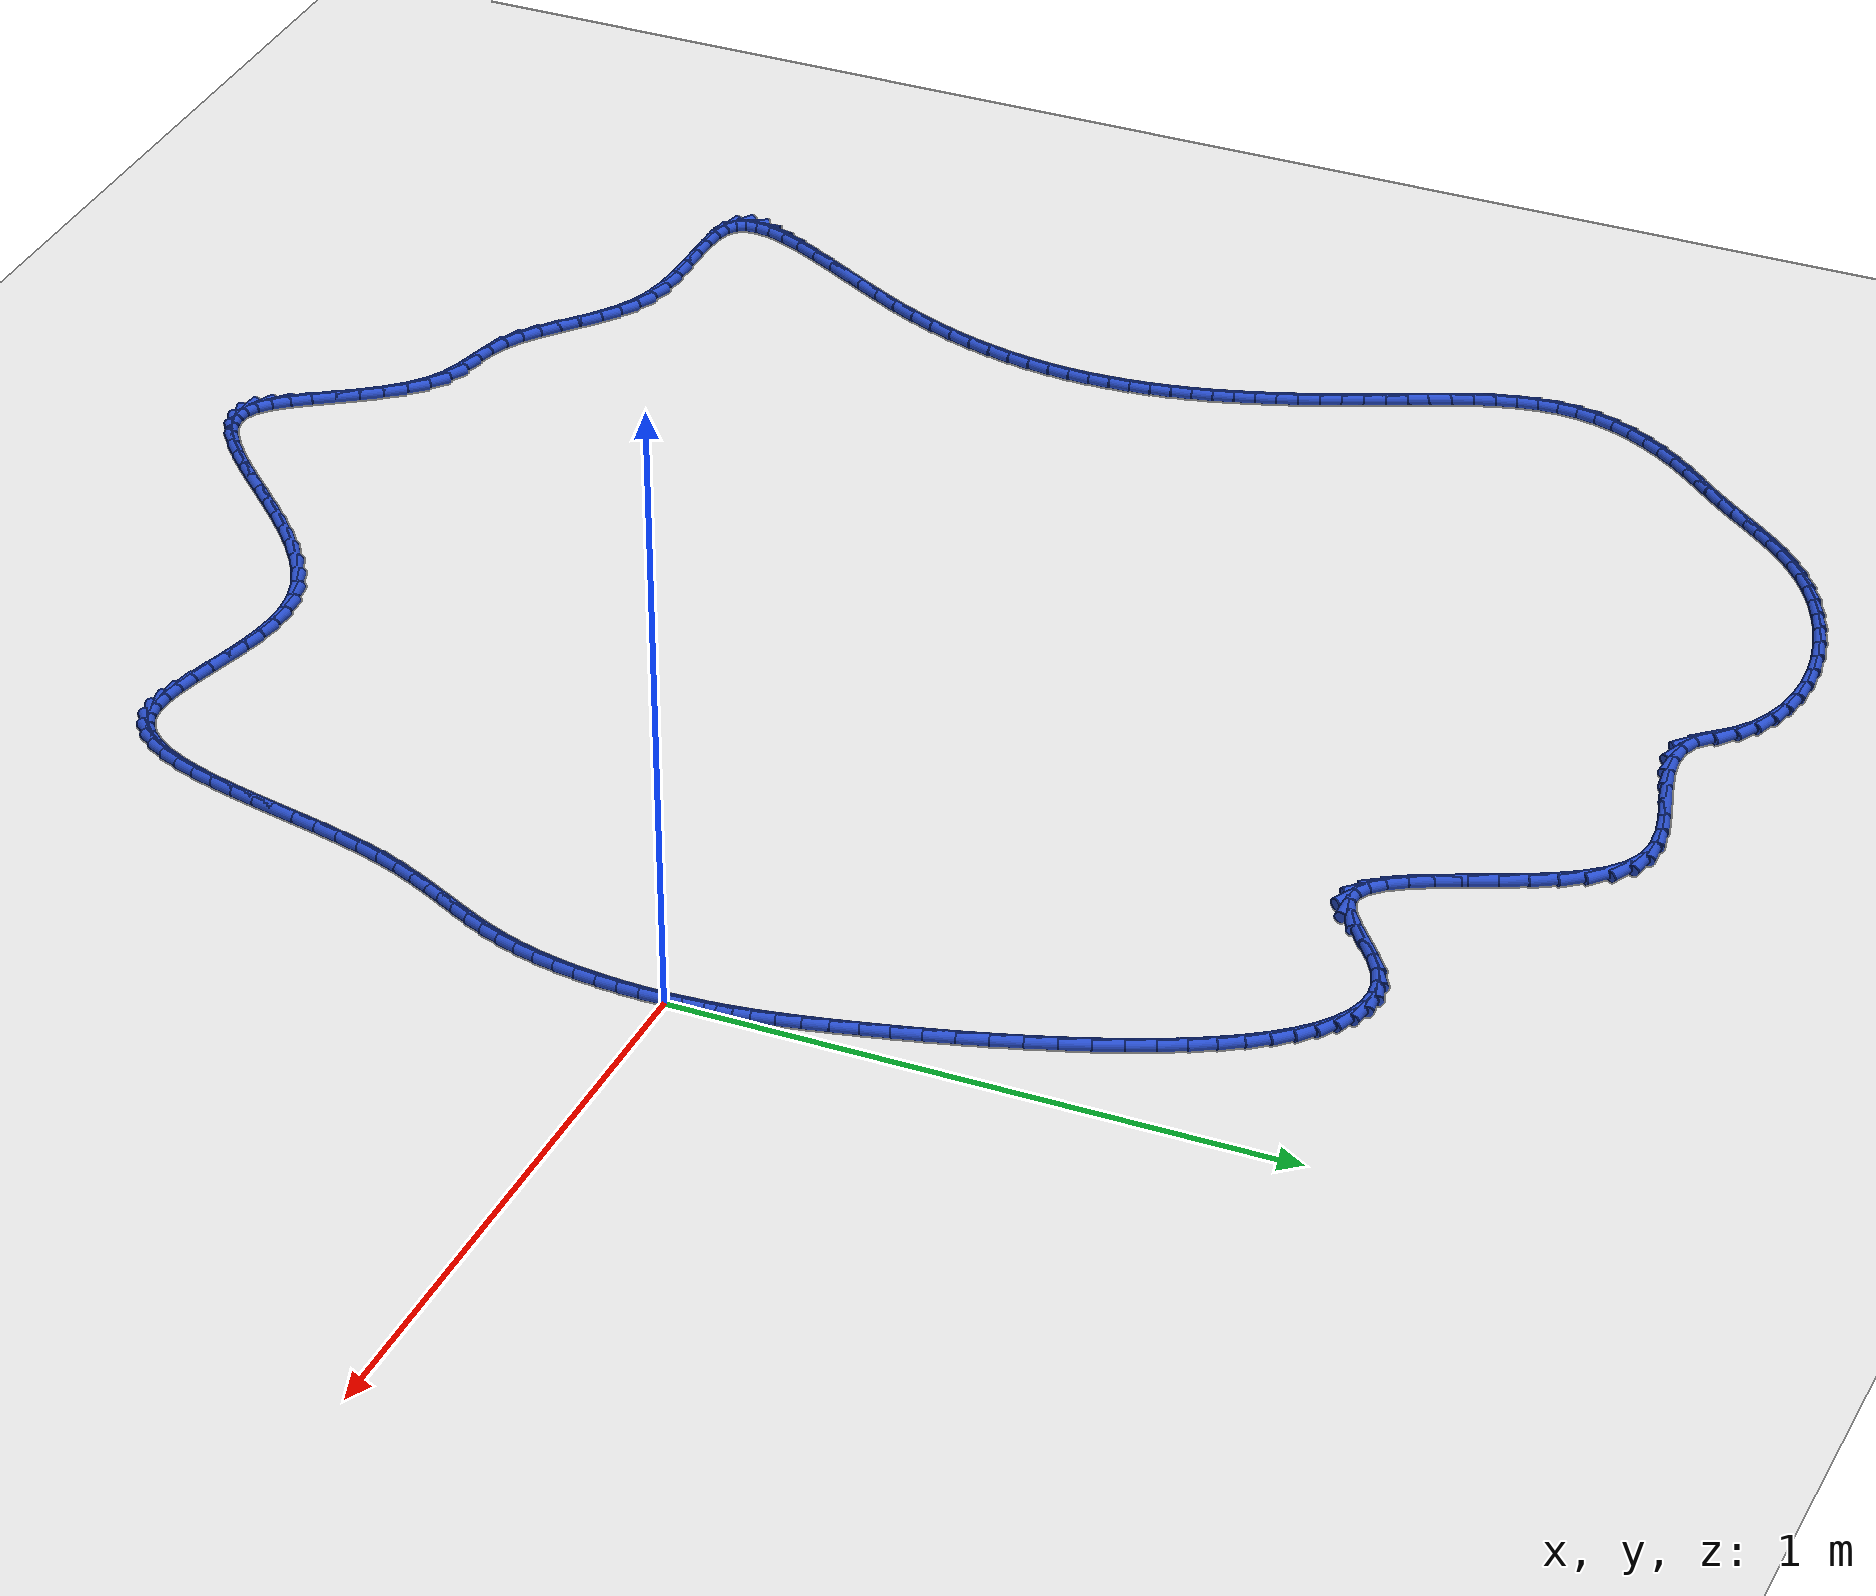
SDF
<sdf version="1.6">
 <world name="default">
  <light name="sun" type="directional">
   <pose>0 0 10 0 -0 0</pose>
   <diffuse>0.8 0.8 0.8 1</diffuse>
   <specular>0.2 0.2 0.2 1</specular>
   <attenuation>
    <range>1000</range>
    <constant>0.9</constant>
    <linear>0.01</linear>
    <quadratic>0.001</quadratic>
   </attenuation>
   <direction>-0.5 0.1 -0.9</direction>
  </light>
  <model name="ground_plane">
   <static>1</static>
   <link name="link">
    <collision name="collision">
     <geometry><plane><normal>0 0 1</normal><size>100 100</size></plane></geometry>
     <surface><friction><ode><mu>100</mu><mu2>50</mu2></ode></friction></surface>
    </collision>
    <visual name="visual">
     <cast_shadows>0</cast_shadows>
     <geometry><plane><normal>0 0 1</normal><size>100 100</size></plane></geometry>
     <material>
      <script><uri>file://media/materials/scripts/gazebo.material</uri><name>Gazebo/WhiteGlow</name></script>
     </material>
    </visual>
   </link>
  </model>
  <gravity>0 0 -9.8</gravity>
  <magnetic_field>6e-06 2.3e-05 -4.2e-05</magnetic_field>
  <atmosphere type="adiabatic"/>
  <physics name="default_physics" default="0" type="ode">
   <max_step_size>0.001</max_step_size>
   <real_time_factor>1</real_time_factor>
   <real_time_update_rate>1000</real_time_update_rate>
  </physics>
  <scene><ambient>0.4 0.4 0.4 1</ambient><background>0.7 0.7 0.7 1</background><shadows>1</shadows></scene>
  <spherical_coordinates>
   <surface_model>EARTH_WGS84</surface_model>
   <latitude_deg>0</latitude_deg>
   <longitude_deg>0</longitude_deg>
   <elevation>0</elevation>
   <heading_deg>0</heading_deg>
  </spherical_coordinates>
  <model name="line">
   <link name="link_0">
    <pose>1.214306433183765e-17 6.245004513516506e-17 0.01 0 1.57 -1.5364172123056168</pose>
    <collision name="collision">
     <geometry><cylinder><radius>0.01</radius><length>0.08</length></cylinder></geometry>
    </collision>
    <visual name="visual">
     <material>
      <script><name>Gazebo/Blue</name><uri>file://media/materials/scripts/gazebo.material</uri></script>
     </material>
     <geometry><cylinder><radius>0.01</radius><length>0.08</length></cylinder></geometry>
    </visual>
   </link>
   <link name="link_1">
    <pose>-0.0011973013457162733 0.0348126942802152 0.01 0 1.57 -1.5012761629877742</pose>
    <collision name="collision">
     <geometry><cylinder><radius>0.01</radius><length>0.08</length></cylinder></geometry>
    </collision>
    <visual name="visual">
     <material>
      <script><name>Gazebo/Blue</name><uri>file://media/materials/scripts/gazebo.material</uri></script>
     </material>
     <geometry><cylinder><radius>0.01</radius><length>0.08</length></cylinder></geometry>
    </visual>
   </link>
   <link name="link_2">
    <pose>-0.003584825711390027 0.06910025419359601 0.01 0 1.57 -1.4670397695237476</pose>
    <collision name="collision">
     <geometry><cylinder><radius>0.01</radius><length>0.08</length></cylinder></geometry>
    </collision>
    <visual name="visual">
     <material>
      <script><name>Gazebo/Blue</name><uri>file://media/materials/scripts/gazebo.material</uri></script>
     </material>
     <geometry><cylinder><radius>0.01</radius><length>0.08</length></cylinder></geometry>
    </visual>
   </link>
   <link name="link_3">
    <pose>-0.007145196230467033 0.10329168396970194 0.01 0 1.57 -1.4350416926073262</pose>
    <collision name="collision">
     <geometry><cylinder><radius>0.01</radius><length>0.08</length></cylinder></geometry>
    </collision>
    <visual name="visual">
     <material>
      <script><name>Gazebo/Blue</name><uri>file://media/materials/scripts/gazebo.material</uri></script>
     </material>
     <geometry><cylinder><radius>0.01</radius><length>0.08</length></cylinder></geometry>
    </visual>
   </link>
   <link name="link_4">
    <pose>-0.011861036036393078 0.13781598783809249 0.01 0 1.57 -1.4063949400747409</pose>
    <collision name="collision">
     <geometry><cylinder><radius>0.01</radius><length>0.08</length></cylinder></geometry>
    </collision>
    <visual name="visual">
     <material>
      <script><name>Gazebo/Blue</name><uri>file://media/materials/scripts/gazebo.material</uri></script>
     </material>
     <geometry><cylinder><radius>0.01</radius><length>0.08</length></cylinder></geometry>
    </visual>
   </link>
   <link name="link_5">
    <pose>-0.017714968262613952 0.17310217002832703 0.01 0 1.57 -1.3818702839190338</pose>
    <collision name="collision">
     <geometry><cylinder><radius>0.01</radius><length>0.08</length></cylinder></geometry>
    </collision>
    <visual name="visual">
     <material>
      <script><name>Gazebo/Blue</name><uri>file://media/materials/scripts/gazebo.material</uri></script>
     </material>
     <geometry><cylinder><radius>0.01</radius><length>0.08</length></cylinder></geometry>
    </visual>
   </link>
   <link name="link_6">
    <pose>-0.024689616042575434 0.20957923476996512 0.01 0 1.57 -1.3618533897870633</pose>
    <collision name="collision">
     <geometry><cylinder><radius>0.01</radius><length>0.08</length></cylinder></geometry>
    </collision>
    <visual name="visual">
     <material>
      <script><name>Gazebo/Blue</name><uri>file://media/materials/scripts/gazebo.material</uri></script>
     </material>
     <geometry><cylinder><radius>0.01</radius><length>0.08</length></cylinder></geometry>
    </visual>
   </link>
   <link name="link_7">
    <pose>-0.03276760250972331 0.24767618629256619 0.01 0 1.57 -1.3463722413783226</pose>
    <collision name="collision">
     <geometry><cylinder><radius>0.01</radius><length>0.08</length></cylinder></geometry>
    </collision>
    <visual name="visual">
     <material>
      <script><name>Gazebo/Blue</name><uri>file://media/materials/scripts/gazebo.material</uri></script>
     </material>
     <geometry><cylinder><radius>0.01</radius><length>0.08</length></cylinder></geometry>
    </visual>
   </link>
   <link name="link_8">
    <pose>-0.04193155645691852 0.2878215377126944 0.01 0 1.57 -1.3339066279676435</pose>
    <collision name="collision">
     <geometry><cylinder><radius>0.01</radius><length>0.08</length></cylinder></geometry>
    </collision>
    <visual name="visual">
     <material>
      <script><name>Gazebo/Blue</name><uri>file://media/materials/scripts/gazebo.material</uri></script>
     </material>
     <geometry><cylinder><radius>0.01</radius><length>0.08</length></cylinder></geometry>
    </visual>
   </link>
   <link name="link_9">
    <pose>-0.05216672301584432 0.3302167613726171 0.01 0 1.57 -1.3208588870401436</pose>
    <collision name="collision">
     <geometry><cylinder><radius>0.01</radius><length>0.08</length></cylinder></geometry>
    </collision>
    <visual name="visual">
     <material>
      <script><name>Gazebo/Blue</name><uri>file://media/materials/scripts/gazebo.material</uri></script>
     </material>
     <geometry><cylinder><radius>0.01</radius><length>0.08</length></cylinder></geometry>
    </visual>
   </link>
   <link name="link_10">
    <pose>-0.06346511105945914 0.37447638535374156 0.01 0 1.57 -1.3064606607210427</pose>
    <collision name="collision">
     <geometry><cylinder><radius>0.01</radius><length>0.08</length></cylinder></geometry>
    </collision>
    <visual name="visual">
     <material>
      <script><name>Gazebo/Blue</name><uri>file://media/materials/scripts/gazebo.material</uri></script>
     </material>
     <geometry><cylinder><radius>0.01</radius><length>0.08</length></cylinder></geometry>
    </visual>
   </link>
   <link name="link_11">
    <pose>-0.07581980790520755 0.42012135243075 0.01 0 1.57 -1.290437660495635</pose>
    <collision name="collision">
     <geometry><cylinder><radius>0.01</radius><length>0.08</length></cylinder></geometry>
    </collision>
    <visual name="visual">
     <material>
      <script><name>Gazebo/Blue</name><uri>file://media/materials/scripts/gazebo.material</uri></script>
     </material>
     <geometry><cylinder><radius>0.01</radius><length>0.08</length></cylinder></geometry>
    </visual>
   </link>
   <link name="link_12">
    <pose>-0.08922390087053418 0.46667260537832467 0.01 0 1.57 -1.2724595972651556</pose>
    <collision name="collision">
     <geometry><cylinder><radius>0.01</radius><length>0.08</length></cylinder></geometry>
    </collision>
    <visual name="visual">
     <material>
      <script><name>Gazebo/Blue</name><uri>file://media/materials/scripts/gazebo.material</uri></script>
     </material>
     <geometry><cylinder><radius>0.01</radius><length>0.08</length></cylinder></geometry>
    </visual>
   </link>
   <link name="link_13">
    <pose>-0.10367047727288366 0.5136510869711479 0.01 0 1.57 -1.2521188784909092</pose>
    <collision name="collision">
     <geometry><cylinder><radius>0.01</radius><length>0.08</length></cylinder></geometry>
    </collision>
    <visual name="visual">
     <material>
      <script><name>Gazebo/Blue</name><uri>file://media/materials/scripts/gazebo.material</uri></script>
     </material>
     <geometry><cylinder><radius>0.01</radius><length>0.08</length></cylinder></geometry>
    </visual>
   </link>
   <link name="link_14">
    <pose>-0.11915262442970051 0.5605777399839015 0.01 0 1.57 -1.2289027898675515</pose>
    <collision name="collision">
     <geometry><cylinder><radius>0.01</radius><length>0.08</length></cylinder></geometry>
    </collision>
    <visual name="visual">
     <material>
      <script><name>Gazebo/Blue</name><uri>file://media/materials/scripts/gazebo.material</uri></script>
     </material>
     <geometry><cylinder><radius>0.01</radius><length>0.08</length></cylinder></geometry>
    </visual>
   </link>
   <link name="link_15">
    <pose>-0.13566342965842945 0.6069735071912683 0.01 0 1.57 -1.2021556669128068</pose>
    <collision name="collision">
     <geometry><cylinder><radius>0.01</radius><length>0.08</length></cylinder></geometry>
    </collision>
    <visual name="visual">
     <material>
      <script><name>Gazebo/Blue</name><uri>file://media/materials/scripts/gazebo.material</uri></script>
     </material>
     <geometry><cylinder><radius>0.01</radius><length>0.08</length></cylinder></geometry>
    </visual>
   </link>
   <link name="link_16">
    <pose>-0.15319598027651504 0.6523593313679301 0.01 0 1.57 -1.1710262550954402</pose>
    <collision name="collision">
     <geometry><cylinder><radius>0.01</radius><length>0.08</length></cylinder></geometry>
    </collision>
    <visual name="visual">
     <material>
      <script><name>Gazebo/Blue</name><uri>file://media/materials/scripts/gazebo.material</uri></script>
     </material>
     <geometry><cylinder><radius>0.01</radius><length>0.08</length></cylinder></geometry>
    </visual>
   </link>
   <link name="link_17">
    <pose>-0.1717433636014019 0.6962561552885697 0.01 0 1.57 -1.1343935214573693</pose>
    <collision name="collision">
     <geometry><cylinder><radius>0.01</radius><length>0.08</length></cylinder></geometry>
    </collision>
    <visual name="visual">
     <material>
      <script><name>Gazebo/Blue</name><uri>file://media/materials/scripts/gazebo.material</uri></script>
     </material>
     <geometry><cylinder><radius>0.01</radius><length>0.08</length></cylinder></geometry>
    </visual>
   </link>
   <link name="link_18">
    <pose>-0.19129866695053468 0.7381849217278688 0.01 0 1.57 -1.0907617606013689</pose>
    <collision name="collision">
     <geometry><cylinder><radius>0.01</radius><length>0.08</length></cylinder></geometry>
    </collision>
    <visual name="visual">
     <material>
      <script><name>Gazebo/Blue</name><uri>file://media/materials/scripts/gazebo.material</uri></script>
     </material>
     <geometry><cylinder><radius>0.01</radius><length>0.08</length></cylinder></geometry>
    </visual>
   </link>
   <link name="link_19">
    <pose>-0.21185497764135788 0.7776665734605097 0.01 0 1.57 -1.038113904352645</pose>
    <collision name="collision">
     <geometry><cylinder><radius>0.01</radius><length>0.08</length></cylinder></geometry>
    </collision>
    <visual name="visual">
     <material>
      <script><name>Gazebo/Blue</name><uri>file://media/materials/scripts/gazebo.material</uri></script>
     </material>
     <geometry><cylinder><radius>0.01</radius><length>0.08</length></cylinder></geometry>
    </visual>
   </link>
   <link name="link_20">
    <pose>-0.23340538299131622 0.8142220532611749 0.01 0 1.57 -0.9737142129901559</pose>
    <collision name="collision">
     <geometry><cylinder><radius>0.01</radius><length>0.08</length></cylinder></geometry>
    </collision>
    <visual name="visual">
     <material>
      <script><name>Gazebo/Blue</name><uri>file://media/materials/scripts/gazebo.material</uri></script>
     </material>
     <geometry><cylinder><radius>0.01</radius><length>0.08</length></cylinder></geometry>
    </visual>
   </link>
   <link name="link_21">
    <pose>-0.2559429703178542 0.8473723039045464 0.01 0 1.57 -0.8938697668677389</pose>
    <collision name="collision">
     <geometry><cylinder><radius>0.01</radius><length>0.08</length></cylinder></geometry>
    </collision>
    <visual name="visual">
     <material>
      <script><name>Gazebo/Blue</name><uri>file://media/materials/scripts/gazebo.material</uri></script>
     </material>
     <geometry><cylinder><radius>0.01</radius><length>0.08</length></cylinder></geometry>
    </visual>
   </link>
   <link name="link_22">
    <pose>-0.27946082693841645 0.8766382681653067 0.01 0 1.57 -0.7937270958802107</pose>
    <collision name="collision">
     <geometry><cylinder><radius>0.01</radius><length>0.08</length></cylinder></geometry>
    </collision>
    <visual name="visual">
     <material>
      <script><name>Gazebo/Blue</name><uri>file://media/materials/scripts/gazebo.material</uri></script>
     </material>
     <geometry><cylinder><radius>0.01</radius><length>0.08</length></cylinder></geometry>
    </visual>
   </link>
   <link name="link_23">
    <pose>-0.30395204017044775 0.9015408888181378 0.01 0 1.57 -0.6673708848554043</pose>
    <collision name="collision">
     <geometry><cylinder><radius>0.01</radius><length>0.08</length></cylinder></geometry>
    </collision>
    <visual name="visual">
     <material>
      <script><name>Gazebo/Blue</name><uri>file://media/materials/scripts/gazebo.material</uri></script>
     </material>
     <geometry><cylinder><radius>0.01</radius><length>0.08</length></cylinder></geometry>
    </visual>
   </link>
   <link name="link_24">
    <pose>-0.32940969733139247 0.9216011086377218 0.01 0 1.57 -0.508905908157725</pose>
    <collision name="collision">
     <geometry><cylinder><radius>0.01</radius><length>0.08</length></cylinder></geometry>
    </collision>
    <visual name="visual">
     <material>
      <script><name>Gazebo/Blue</name><uri>file://media/materials/scripts/gazebo.material</uri></script>
     </material>
     <geometry><cylinder><radius>0.01</radius><length>0.08</length></cylinder></geometry>
    </visual>
   </link>
   <link name="link_25">
    <pose>-0.3558268857386955 0.9363398703987417 0.01 0 1.57 -0.3156541800569162</pose>
    <collision name="collision">
     <geometry><cylinder><radius>0.01</radius><length>0.08</length></cylinder></geometry>
    </collision>
    <visual name="visual">
     <material>
      <script><name>Gazebo/Blue</name><uri>file://media/materials/scripts/gazebo.material</uri></script>
     </material>
     <geometry><cylinder><radius>0.01</radius><length>0.08</length></cylinder></geometry>
    </visual>
   </link>
   <link name="link_26">
    <pose>-0.38319669270980106 0.9452781168758788 0.01 0 1.57 -0.0936201269277796</pose>
    <collision name="collision">
     <geometry><cylinder><radius>0.01</radius><length>0.08</length></cylinder></geometry>
    </collision>
    <visual name="visual">
     <material>
      <script><name>Gazebo/Blue</name><uri>file://media/materials/scripts/gazebo.material</uri></script>
     </material>
     <geometry><cylinder><radius>0.01</radius><length>0.08</length></cylinder></geometry>
    </visual>
   </link>
   <link name="link_27">
    <pose>-0.41151220556215407 0.9479367908438159 0.01 0 1.57 0.13924187401673205</pose>
    <collision name="collision">
     <geometry><cylinder><radius>0.01</radius><length>0.08</length></cylinder></geometry>
    </collision>
    <visual name="visual">
     <material>
      <script><name>Gazebo/Blue</name><uri>file://media/materials/scripts/gazebo.material</uri></script>
     </material>
     <geometry><cylinder><radius>0.01</radius><length>0.08</length></cylinder></geometry>
    </visual>
   </link>
   <link name="link_28">
    <pose>-0.44076651161319924 0.9438368350772357 0.01 0 1.57 0.3592882050954425</pose>
    <collision name="collision">
     <geometry><cylinder><radius>0.01</radius><length>0.08</length></cylinder></geometry>
    </collision>
    <visual name="visual">
     <material>
      <script><name>Gazebo/Blue</name><uri>file://media/materials/scripts/gazebo.material</uri></script>
     </material>
     <geometry><cylinder><radius>0.01</radius><length>0.08</length></cylinder></geometry>
    </visual>
   </link>
   <link name="link_29">
    <pose>-0.4709526981803809 0.9324991923508192 0.01 0 1.57 0.5460162304907881</pose>
    <collision name="collision">
     <geometry><cylinder><radius>0.01</radius><length>0.08</length></cylinder></geometry>
    </collision>
    <visual name="visual">
     <material>
      <script><name>Gazebo/Blue</name><uri>file://media/materials/scripts/gazebo.material</uri></script>
     </material>
     <geometry><cylinder><radius>0.01</radius><length>0.08</length></cylinder></geometry>
    </visual>
   </link>
   <link name="link_30">
    <pose>-0.5020363328550971 0.9136116171520401 0.01 0 1.57 0.6529358614871058</pose>
    <collision name="collision">
     <geometry><cylinder><radius>0.01</radius><length>0.08</length></cylinder></geometry>
    </collision>
    <visual name="visual">
     <material>
      <script><name>Gazebo/Blue</name><uri>file://media/materials/scripts/gazebo.material</uri></script>
     </material>
     <geometry><cylinder><radius>0.01</radius><length>0.08</length></cylinder></geometry>
    </visual>
   </link>
   <link name="link_31">
    <pose>-0.5335458336221084 0.8895116604999899 0.01 0 1.57 0.6740015224264819</pose>
    <collision name="collision">
     <geometry><cylinder><radius>0.01</radius><length>0.08</length></cylinder></geometry>
    </collision>
    <visual name="visual">
     <material>
      <script><name>Gazebo/Blue</name><uri>file://media/materials/scripts/gazebo.material</uri></script>
     </material>
     <geometry><cylinder><radius>0.01</radius><length>0.08</length></cylinder></geometry>
    </visual>
   </link>
   <link name="link_32">
    <pose>-0.5646596316467588 0.8646583298811094 0.01 0 1.57 0.6144774149631613</pose>
    <collision name="collision">
     <geometry><cylinder><radius>0.01</radius><length>0.08</length></cylinder></geometry>
    </collision>
    <visual name="visual">
     <material>
      <script><name>Gazebo/Blue</name><uri>file://media/materials/scripts/gazebo.material</uri></script>
     </material>
     <geometry><cylinder><radius>0.01</radius><length>0.08</length></cylinder></geometry>
    </visual>
   </link>
   <link name="link_33">
    <pose>-0.5945463416170143 0.8435701356781351 0.01 0 1.57 0.43124427876669924</pose>
    <collision name="collision">
     <geometry><cylinder><radius>0.01</radius><length>0.08</length></cylinder></geometry>
    </collision>
    <visual name="visual">
     <material>
      <script><name>Gazebo/Blue</name><uri>file://media/materials/scripts/gazebo.material</uri></script>
     </material>
     <geometry><cylinder><radius>0.01</radius><length>0.08</length></cylinder></geometry>
    </visual>
   </link>
   <link name="link_34">
    <pose>-0.622374578220841 0.8307655882738022 0.01 0 1.57 0.025799011337979936</pose>
    <collision name="collision">
     <geometry><cylinder><radius>0.01</radius><length>0.08</length></cylinder></geometry>
    </collision>
    <visual name="visual">
     <material>
      <script><name>Gazebo/Blue</name><uri>file://media/materials/scripts/gazebo.material</uri></script>
     </material>
     <geometry><cylinder><radius>0.01</radius><length>0.08</length></cylinder></geometry>
    </visual>
   </link>
   <link name="link_35">
    <pose>-0.6474519369915235 0.8301184736333873 0.01 0 1.57 -0.46246767152065776</pose>
    <collision name="collision">
     <geometry><cylinder><radius>0.01</radius><length>0.08</length></cylinder></geometry>
    </collision>
    <visual name="visual">
     <material>
      <script><name>Gazebo/Blue</name><uri>file://media/materials/scripts/gazebo.material</uri></script>
     </material>
     <geometry><cylinder><radius>0.01</radius><length>0.08</length></cylinder></geometry>
    </visual>
   </link>
   <link name="link_36">
    <pose>-0.6699811924695077 0.8413498920582518 0.01 0 1.57 -0.8008854762243441</pose>
    <collision name="collision">
     <geometry><cylinder><radius>0.01</radius><length>0.08</length></cylinder></geometry>
    </collision>
    <visual name="visual">
     <material>
      <script><name>Gazebo/Blue</name><uri>file://media/materials/scripts/gazebo.material</uri></script>
     </material>
     <geometry><cylinder><radius>0.01</radius><length>0.08</length></cylinder></geometry>
    </visual>
   </link>
   <link name="link_37">
    <pose>-0.690519952354935 0.8625348925420716 0.01 0 1.57 -0.9915245121324601</pose>
    <collision name="collision">
     <geometry><cylinder><radius>0.01</radius><length>0.08</length></cylinder></geometry>
    </collision>
    <visual name="visual">
     <material>
      <script><name>Gazebo/Blue</name><uri>file://media/materials/scripts/gazebo.material</uri></script>
     </material>
     <geometry><cylinder><radius>0.01</radius><length>0.08</length></cylinder></geometry>
    </visual>
   </link>
   <link name="link_38">
    <pose>-0.7096267136608638 0.8917443986053252 0.01 0 1.57 -1.0940749085628287</pose>
    <collision name="collision">
     <geometry><cylinder><radius>0.01</radius><length>0.08</length></cylinder></geometry>
    </collision>
    <visual name="visual">
     <material>
      <script><name>Gazebo/Blue</name><uri>file://media/materials/scripts/gazebo.material</uri></script>
     </material>
     <geometry><cylinder><radius>0.01</radius><length>0.08</length></cylinder></geometry>
    </visual>
   </link>
   <link name="link_39">
    <pose>-0.7278599734003521 0.9270493337684909 0.01 0 1.57 -1.1446568898654506</pose>
    <collision name="collision">
     <geometry><cylinder><radius>0.01</radius><length>0.08</length></cylinder></geometry>
    </collision>
    <visual name="visual">
     <material>
      <script><name>Gazebo/Blue</name><uri>file://media/materials/scripts/gazebo.material</uri></script>
     </material>
     <geometry><cylinder><radius>0.01</radius><length>0.08</length></cylinder></geometry>
    </visual>
   </link>
   <link name="link_40">
    <pose>-0.7457782285864589 0.9665206215520472 0.01 0 1.57 -1.1601128038462551</pose>
    <collision name="collision">
     <geometry><cylinder><radius>0.01</radius><length>0.08</length></cylinder></geometry>
    </collision>
    <visual name="visual">
     <material>
      <script><name>Gazebo/Blue</name><uri>file://media/materials/scripts/gazebo.material</uri></script>
     </material>
     <geometry><cylinder><radius>0.01</radius><length>0.08</length></cylinder></geometry>
    </visual>
   </link>
   <link name="link_41">
    <pose>-0.7639399762322421 1.0082291854764724 0.01 0 1.57 -1.1468307688760793</pose>
    <collision name="collision">
     <geometry><cylinder><radius>0.01</radius><length>0.08</length></cylinder></geometry>
    </collision>
    <visual name="visual">
     <material>
      <script><name>Gazebo/Blue</name><uri>file://media/materials/scripts/gazebo.material</uri></script>
     </material>
     <geometry><cylinder><radius>0.01</radius><length>0.08</length></cylinder></geometry>
    </visual>
   </link>
   <link name="link_42">
    <pose>-0.7829037133507601 1.0502459490622456 0.01 0 1.57 -1.1046509931713098</pose>
    <collision name="collision">
     <geometry><cylinder><radius>0.01</radius><length>0.08</length></cylinder></geometry>
    </collision>
    <visual name="visual">
     <material>
      <script><name>Gazebo/Blue</name><uri>file://media/materials/scripts/gazebo.material</uri></script>
     </material>
     <geometry><cylinder><radius>0.01</radius><length>0.08</length></cylinder></geometry>
    </visual>
   </link>
   <link name="link_43">
    <pose>-0.8032279369550712 1.0906418358298449 0.01 0 1.57 -1.027674262859565</pose>
    <collision name="collision">
     <geometry><cylinder><radius>0.01</radius><length>0.08</length></cylinder></geometry>
    </collision>
    <visual name="visual">
     <material>
      <script><name>Gazebo/Blue</name><uri>file://media/materials/scripts/gazebo.material</uri></script>
     </material>
     <geometry><cylinder><radius>0.01</radius><length>0.08</length></cylinder></geometry>
    </visual>
   </link>
   <link name="link_44">
    <pose>-0.8254711440582341 1.1274877692997483 0.01 0 1.57 -0.9033452468517789</pose>
    <collision name="collision">
     <geometry><cylinder><radius>0.01</radius><length>0.08</length></cylinder></geometry>
    </collision>
    <visual name="visual">
     <material>
      <script><name>Gazebo/Blue</name><uri>file://media/materials/scripts/gazebo.material</uri></script>
     </material>
     <geometry><cylinder><radius>0.01</radius><length>0.08</length></cylinder></geometry>
    </visual>
   </link>
   <link name="link_45">
    <pose>-0.8501918316733068 1.158854672992435 0.01 0 1.57 -0.7120919974918782</pose>
    <collision name="collision">
     <geometry><cylinder><radius>0.01</radius><length>0.08</length></cylinder></geometry>
    </collision>
    <visual name="visual">
     <material>
      <script><name>Gazebo/Blue</name><uri>file://media/materials/scripts/gazebo.material</uri></script>
     </material>
     <geometry><cylinder><radius>0.01</radius><length>0.08</length></cylinder></geometry>
    </visual>
   </link>
   <link name="link_46">
    <pose>-0.877948496813348 1.1828134704283835 0.01 0 1.57 -0.43663035116877313</pose>
    <collision name="collision">
     <geometry><cylinder><radius>0.01</radius><length>0.08</length></cylinder></geometry>
    </collision>
    <visual name="visual">
     <material>
      <script><name>Gazebo/Blue</name><uri>file://media/materials/scripts/gazebo.material</uri></script>
     </material>
     <geometry><cylinder><radius>0.01</radius><length>0.08</length></cylinder></geometry>
    </visual>
   </link>
   <link name="link_47">
    <pose>-0.9092969047435241 1.1974428492938922 0.01 0 1.57 -0.13273279161382598</pose>
    <collision name="collision">
     <geometry><cylinder><radius>0.01</radius><length>0.08</length></cylinder></geometry>
    </collision>
    <visual name="visual">
     <material>
      <script><name>Gazebo/Blue</name><uri>file://media/materials/scripts/gazebo.material</uri></script>
     </material>
     <geometry><cylinder><radius>0.01</radius><length>0.08</length></cylinder></geometry>
    </visual>
   </link>
   <link name="link_48">
    <pose>-0.9443355560453697 1.2021211336139008 0.01 0 1.57 0.08297728606541009</pose>
    <collision name="collision">
     <geometry><cylinder><radius>0.01</radius><length>0.08</length></cylinder></geometry>
    </collision>
    <visual name="visual">
     <material>
      <script><name>Gazebo/Blue</name><uri>file://media/materials/scripts/gazebo.material</uri></script>
     </material>
     <geometry><cylinder><radius>0.01</radius><length>0.08</length></cylinder></geometry>
    </visual>
   </link>
   <link name="link_49">
    <pose>-0.982196930347747 1.1989722693231921 0.01 0 1.57 0.21103295944063138</pose>
    <collision name="collision">
     <geometry><cylinder><radius>0.01</radius><length>0.08</length></cylinder></geometry>
    </collision>
    <visual name="visual">
     <material>
      <script><name>Gazebo/Blue</name><uri>file://media/materials/scripts/gazebo.material</uri></script>
     </material>
     <geometry><cylinder><radius>0.01</radius><length>0.08</length></cylinder></geometry>
    </visual>
   </link>
   <link name="link_50">
    <pose>-1.0218908053405618 1.1904689454464856 0.01 0 1.57 0.27380852703204606</pose>
    <collision name="collision">
     <geometry><cylinder><radius>0.01</radius><length>0.08</length></cylinder></geometry>
    </collision>
    <visual name="visual">
     <material>
      <script><name>Gazebo/Blue</name><uri>file://media/materials/scripts/gazebo.material</uri></script>
     </material>
     <geometry><cylinder><radius>0.01</radius><length>0.08</length></cylinder></geometry>
    </visual>
   </link>
   <link name="link_51">
    <pose>-1.0624269587137192 1.1790838510085022 0.01 0 1.57 0.2841199624350879</pose>
    <collision name="collision">
     <geometry><cylinder><radius>0.01</radius><length>0.08</length></cylinder></geometry>
    </collision>
    <visual name="visual">
     <material>
      <script><name>Gazebo/Blue</name><uri>file://media/materials/scripts/gazebo.material</uri></script>
     </material>
     <geometry><cylinder><radius>0.01</radius><length>0.08</length></cylinder></geometry>
    </visual>
   </link>
   <link name="link_52">
    <pose>-1.102815168157126 1.1672896750339625 0.01 0 1.57 0.24301280588141128</pose>
    <collision name="collision">
     <geometry><cylinder><radius>0.01</radius><length>0.08</length></cylinder></geometry>
    </collision>
    <visual name="visual">
     <material>
      <script><name>Gazebo/Blue</name><uri>file://media/materials/scripts/gazebo.material</uri></script>
     </material>
     <geometry><cylinder><radius>0.01</radius><length>0.08</length></cylinder></geometry>
    </visual>
   </link>
   <link name="link_53">
    <pose>-1.1420652113606875 1.1575591065475865 0.01 0 1.57 0.13902302836025154</pose>
    <collision name="collision">
     <geometry><cylinder><radius>0.01</radius><length>0.08</length></cylinder></geometry>
    </collision>
    <visual name="visual">
     <material>
      <script><name>Gazebo/Blue</name><uri>file://media/materials/scripts/gazebo.material</uri></script>
     </material>
     <geometry><cylinder><radius>0.01</radius><length>0.08</length></cylinder></geometry>
    </visual>
   </link>
   <link name="link_54">
    <pose>-1.1791868660143092 1.1523648345740942 0.01 0 1.57 -0.0533185671387295</pose>
    <collision name="collision">
     <geometry><cylinder><radius>0.01</radius><length>0.08</length></cylinder></geometry>
    </collision>
    <visual name="visual">
     <material>
      <script><name>Gazebo/Blue</name><uri>file://media/materials/scripts/gazebo.material</uri></script>
     </material>
     <geometry><cylinder><radius>0.01</radius><length>0.08</length></cylinder></geometry>
    </visual>
   </link>
   <link name="link_55">
    <pose>-1.2131899098078975 1.1541795481382067 0.01 0 1.57 -0.36129214879909916</pose>
    <collision name="collision">
     <geometry><cylinder><radius>0.01</radius><length>0.08</length></cylinder></geometry>
    </collision>
    <visual name="visual">
     <material>
      <script><name>Gazebo/Blue</name><uri>file://media/materials/scripts/gazebo.material</uri></script>
     </material>
     <geometry><cylinder><radius>0.01</radius><length>0.08</length></cylinder></geometry>
    </visual>
   </link>
   <link name="link_56">
    <pose>-1.2430841204313574 1.1654759362646439 0.01 0 1.57 -0.7477746549677848</pose>
    <collision name="collision">
     <geometry><cylinder><radius>0.01</radius><length>0.08</length></cylinder></geometry>
    </collision>
    <visual name="visual">
     <material>
      <script><name>Gazebo/Blue</name><uri>file://media/materials/scripts/gazebo.material</uri></script>
     </material>
     <geometry><cylinder><radius>0.01</radius><length>0.08</length></cylinder></geometry>
    </visual>
   </link>
   <link name="link_57">
    <pose>-1.2679685971139445 1.1885550041734565 0.01 0 1.57 -0.8473288829064564</pose>
    <collision name="collision">
     <geometry><cylinder><radius>0.01</radius><length>0.08</length></cylinder></geometry>
    </collision>
    <visual name="visual">
     <material>
      <script><name>Gazebo/Blue</name><uri>file://media/materials/scripts/gazebo.material</uri></script>
     </material>
     <geometry><cylinder><radius>0.01</radius><length>0.08</length></cylinder></geometry>
    </visual>
   </link>
   <link name="link_58">
    <pose>-1.2920571512433392 1.215828521253727 0.01 0 1.57 -0.6626221886639944</pose>
    <collision name="collision">
     <geometry><cylinder><radius>0.01</radius><length>0.08</length></cylinder></geometry>
    </collision>
    <visual name="visual">
     <material>
      <script><name>Gazebo/Blue</name><uri>file://media/materials/scripts/gazebo.material</uri></script>
     </material>
     <geometry><cylinder><radius>0.01</radius><length>0.08</length></cylinder></geometry>
    </visual>
   </link>
   <link name="link_59">
    <pose>-1.320169652873955 1.2377651314889422 0.01 0 1.57 -0.48386697379064536</pose>
    <collision name="collision">
     <geometry><cylinder><radius>0.01</radius><length>0.08</length></cylinder></geometry>
    </collision>
    <visual name="visual">
     <material>
      <script><name>Gazebo/Blue</name><uri>file://media/materials/scripts/gazebo.material</uri></script>
     </material>
     <geometry><cylinder><radius>0.01</radius><length>0.08</length></cylinder></geometry>
    </visual>
   </link>
   <link name="link_60">
    <pose>-1.3518523797611735 1.2544155401432862 0.01 0 1.57 -0.32429105688157894</pose>
    <collision name="collision">
     <geometry><cylinder><radius>0.01</radius><length>0.08</length></cylinder></geometry>
    </collision>
    <visual name="visual">
     <material>
      <script><name>Gazebo/Blue</name><uri>file://media/materials/scripts/gazebo.material</uri></script>
     </material>
     <geometry><cylinder><radius>0.01</radius><length>0.08</length></cylinder></geometry>
    </visual>
   </link>
   <link name="link_61">
    <pose>-1.386520961216939 1.2660696789127641 0.01 0 1.57 -0.18527402597767326</pose>
    <collision name="collision">
     <geometry><cylinder><radius>0.01</radius><length>0.08</length></cylinder></geometry>
    </collision>
    <visual name="visual">
     <material>
      <script><name>Gazebo/Blue</name><uri>file://media/materials/scripts/gazebo.material</uri></script>
     </material>
     <geometry><cylinder><radius>0.01</radius><length>0.08</length></cylinder></geometry>
    </visual>
   </link>
   <link name="link_62">
    <pose>-1.423591026553195 1.2730174794933786 0.01 0 1.57 -0.0650041396111466</pose>
    <collision name="collision">
     <geometry><cylinder><radius>0.01</radius><length>0.08</length></cylinder></geometry>
    </collision>
    <visual name="visual">
     <material>
      <script><name>Gazebo/Blue</name><uri>file://media/materials/scripts/gazebo.material</uri></script>
     </material>
     <geometry><cylinder><radius>0.01</radius><length>0.08</length></cylinder></geometry>
    </visual>
   </link>
   <link name="link_63">
    <pose>-1.4624782050818865 1.2755488735811338 0.01 0 1.57 0.039736894402182935</pose>
    <collision name="collision">
     <geometry><cylinder><radius>0.01</radius><length>0.08</length></cylinder></geometry>
    </collision>
    <visual name="visual">
     <material>
      <script><name>Gazebo/Blue</name><uri>file://media/materials/scripts/gazebo.material</uri></script>
     </material>
     <geometry><cylinder><radius>0.01</radius><length>0.08</length></cylinder></geometry>
    </visual>
   </link>
   <link name="link_64">
    <pose>-1.502598126114957 1.2739537928720337 0.01 0 1.57 0.13245154870885104</pose>
    <collision name="collision">
     <geometry><cylinder><radius>0.01</radius><length>0.08</length></cylinder></geometry>
    </collision>
    <visual name="visual">
     <material>
      <script><name>Gazebo/Blue</name><uri>file://media/materials/scripts/gazebo.material</uri></script>
     </material>
     <geometry><cylinder><radius>0.01</radius><length>0.08</length></cylinder></geometry>
    </visual>
   </link>
   <link name="link_65">
    <pose>-1.5433664189643514 1.2685221690620816 0.01 0 1.57 0.216436552488493</pose>
    <collision name="collision">
     <geometry><cylinder><radius>0.01</radius><length>0.08</length></cylinder></geometry>
    </collision>
    <visual name="visual">
     <material>
      <script><name>Gazebo/Blue</name><uri>file://media/materials/scripts/gazebo.material</uri></script>
     </material>
     <geometry><cylinder><radius>0.01</radius><length>0.08</length></cylinder></geometry>
    </visual>
   </link>
   <link name="link_66">
    <pose>-1.5841987129420136 1.259543933847281 0.01 0 1.57 0.2946702870413316</pose>
    <collision name="collision">
     <geometry><cylinder><radius>0.01</radius><length>0.08</length></cylinder></geometry>
    </collision>
    <visual name="visual">
     <material>
      <script><name>Gazebo/Blue</name><uri>file://media/materials/scripts/gazebo.material</uri></script>
     </material>
     <geometry><cylinder><radius>0.01</radius><length>0.08</length></cylinder></geometry>
    </visual>
   </link>
   <link name="link_67">
    <pose>-1.6245106373598877 1.2473090189236369 0.01 0 1.57 0.3698811734518021</pose>
    <collision name="collision">
     <geometry><cylinder><radius>0.01</radius><length>0.08</length></cylinder></geometry>
    </collision>
    <visual name="visual">
     <material>
      <script><name>Gazebo/Blue</name><uri>file://media/materials/scripts/gazebo.material</uri></script>
     </material>
     <geometry><cylinder><radius>0.01</radius><length>0.08</length></cylinder></geometry>
    </visual>
   </link>
   <link name="link_68">
    <pose>-1.6637178215299178 1.232107355987151 0.01 0 1.57 0.4446957608849422</pose>
    <collision name="collision">
     <geometry><cylinder><radius>0.01</radius><length>0.08</length></cylinder></geometry>
    </collision>
    <visual name="visual">
     <material>
      <script><name>Gazebo/Blue</name><uri>file://media/materials/scripts/gazebo.material</uri></script>
     </material>
     <geometry><cylinder><radius>0.01</radius><length>0.08</length></cylinder></geometry>
    </visual>
   </link>
   <link name="link_69">
    <pose>-1.7012358947640482 1.2142288767338294 0.01 0 1.57 0.5218283881655081</pose>
    <collision name="collision">
     <geometry><cylinder><radius>0.01</radius><length>0.08</length></cylinder></geometry>
    </collision>
    <visual name="visual">
     <material>
      <script><name>Gazebo/Blue</name><uri>file://media/materials/scripts/gazebo.material</uri></script>
     </material>
     <geometry><cylinder><radius>0.01</radius><length>0.08</length></cylinder></geometry>
    </visual>
   </link>
   <link name="link_70">
    <pose>-1.736480486374223 1.1939635128596735 0.01 0 1.57 0.6042747989689048</pose>
    <collision name="collision">
     <geometry><cylinder><radius>0.01</radius><length>0.08</length></cylinder></geometry>
    </collision>
    <visual name="visual">
     <material>
      <script><name>Gazebo/Blue</name><uri>file://media/materials/scripts/gazebo.material</uri></script>
     </material>
     <geometry><cylinder><radius>0.01</radius><length>0.08</length></cylinder></geometry>
    </visual>
   </link>
   <link name="link_71">
    <pose>-1.768869307492859 1.1716012717804636 0.01 0 1.57 0.689600823613114</pose>
    <collision name="collision">
     <geometry><cylinder><radius>0.01</radius><length>0.08</length></cylinder></geometry>
    </collision>
    <visual name="visual">
     <material>
      <script><name>Gazebo/Blue</name><uri>file://media/materials/scripts/gazebo.material</uri></script>
     </material>
     <geometry><cylinder><radius>0.01</radius><length>0.08</length></cylinder></geometry>
    </visual>
   </link>
   <link name="link_72">
    <pose>-1.798162010369089 1.147444597961484 0.01 0 1.57 0.7652700643637813</pose>
    <collision name="collision">
     <geometry><cylinder><radius>0.01</radius><length>0.08</length></cylinder></geometry>
    </collision>
    <visual name="visual">
     <material>
      <script><name>Gazebo/Blue</name><uri>file://media/materials/scripts/gazebo.material</uri></script>
     </material>
     <geometry><cylinder><radius>0.01</radius><length>0.08</length></cylinder></geometry>
    </visual>
   </link>
   <link name="link_73">
    <pose>-1.824837316314378 1.1218220897790019 0.01 0 1.57 0.8268070320742029</pose>
    <collision name="collision">
     <geometry><cylinder><radius>0.01</radius><length>0.08</length></cylinder></geometry>
    </collision>
    <visual name="visual">
     <material>
      <script><name>Gazebo/Blue</name><uri>file://media/materials/scripts/gazebo.material</uri></script>
     </material>
     <geometry><cylinder><radius>0.01</radius><length>0.08</length></cylinder></geometry>
    </visual>
   </link>
   <link name="link_74">
    <pose>-1.8494647896484935 1.095065649742469 0.01 0 1.57 0.8721345711113417</pose>
    <collision name="collision">
     <geometry><cylinder><radius>0.01</radius><length>0.08</length></cylinder></geometry>
    </collision>
    <visual name="visual">
     <material>
      <script><name>Gazebo/Blue</name><uri>file://media/materials/scripts/gazebo.material</uri></script>
     </material>
     <geometry><cylinder><radius>0.01</radius><length>0.08</length></cylinder></geometry>
    </visual>
   </link>
   <link name="link_75">
    <pose>-1.8726139946912017 1.067507180361339 0.01 0 1.57 0.9000355454267183</pose>
    <collision name="collision">
     <geometry><cylinder><radius>0.01</radius><length>0.08</length></cylinder></geometry>
    </collision>
    <visual name="visual">
     <material>
      <script><name>Gazebo/Blue</name><uri>file://media/materials/scripts/gazebo.material</uri></script>
     </material>
     <geometry><cylinder><radius>0.01</radius><length>0.08</length></cylinder></geometry>
    </visual>
   </link>
   <link name="link_76">
    <pose>-1.894854495762269 1.039478584145064 0.01 0 1.57 0.9098895628897574</pose>
    <collision name="collision">
     <geometry><cylinder><radius>0.01</radius><length>0.08</length></cylinder></geometry>
    </collision>
    <visual name="visual">
     <material>
      <script><name>Gazebo/Blue</name><uri>file://media/materials/scripts/gazebo.material</uri></script>
     </material>
     <geometry><cylinder><radius>0.01</radius><length>0.08</length></cylinder></geometry>
    </visual>
   </link>
   <link name="link_77">
    <pose>-1.916755857181462 1.0113117636030977 0.01 0 1.57 0.9014567225173544</pose>
    <collision name="collision">
     <geometry><cylinder><radius>0.01</radius><length>0.08</length></cylinder></geometry>
    </collision>
    <visual name="visual">
     <material>
      <script><name>Gazebo/Blue</name><uri>file://media/materials/scripts/gazebo.material</uri></script>
     </material>
     <geometry><cylinder><radius>0.01</radius><length>0.08</length></cylinder></geometry>
    </visual>
   </link>
   <link name="link_78">
    <pose>-1.9388876432685467 0.9833386212448918 0.01 0 1.57 0.8754460328419026</pose>
    <collision name="collision">
     <geometry><cylinder><radius>0.01</radius><length>0.08</length></cylinder></geometry>
    </collision>
    <visual name="visual">
     <material>
      <script><name>Gazebo/Blue</name><uri>file://media/materials/scripts/gazebo.material</uri></script>
     </material>
     <geometry><cylinder><radius>0.01</radius><length>0.08</length></cylinder></geometry>
    </visual>
   </link>
   <link name="link_79">
    <pose>-1.961802112907573 0.9558754512818184 0.01 0 1.57 0.8539113630981349</pose>
    <collision name="collision">
     <geometry><cylinder><radius>0.01</radius><length>0.08</length></cylinder></geometry>
    </collision>
    <visual name="visual">
     <material>
      <script><name>Gazebo/Blue</name><uri>file://media/materials/scripts/gazebo.material</uri></script>
     </material>
     <geometry><cylinder><radius>0.01</radius><length>0.08</length></cylinder></geometry>
    </visual>
   </link>
   <link name="link_80">
    <pose>-1.9854729209427042 0.9287166873680643 0.01 0 1.57 0.862938002096297</pose>
    <collision name="collision">
     <geometry><cylinder><radius>0.01</radius><length>0.08</length></cylinder></geometry>
    </collision>
    <visual name="visual">
     <material>
      <script><name>Gazebo/Blue</name><uri>file://media/materials/scripts/gazebo.material</uri></script>
     </material>
     <geometry><cylinder><radius>0.01</radius><length>0.08</length></cylinder></geometry>
    </visual>
   </link>
   <link name="link_81">
    <pose>-2.0091724314570736 0.9010242477205379 0.01 0 1.57 0.9018559592327918</pose>
    <collision name="collision">
     <geometry><cylinder><radius>0.01</radius><length>0.08</length></cylinder></geometry>
    </collision>
    <visual name="visual">
     <material>
      <script><name>Gazebo/Blue</name><uri>file://media/materials/scripts/gazebo.material</uri></script>
     </material>
     <geometry><cylinder><radius>0.01</radius><length>0.08</length></cylinder></geometry>
    </visual>
   </link>
   <link name="link_82">
    <pose>-2.032140442566397 0.8719703406169557 0.01 0 1.57 0.9564129762920881</pose>
    <collision name="collision">
     <geometry><cylinder><radius>0.01</radius><length>0.08</length></cylinder></geometry>
    </collision>
    <visual name="visual">
     <material>
      <script><name>Gazebo/Blue</name><uri>file://media/materials/scripts/gazebo.material</uri></script>
     </material>
     <geometry><cylinder><radius>0.01</radius><length>0.08</length></cylinder></geometry>
    </visual>
   </link>
   <link name="link_83">
    <pose>-2.053740498691467 0.8413520937504657 0.01 0 1.57 1.0186775631879026</pose>
    <collision name="collision">
     <geometry><cylinder><radius>0.01</radius><length>0.08</length></cylinder></geometry>
    </collision>
    <visual name="visual">
     <material>
      <script><name>Gazebo/Blue</name><uri>file://media/materials/scripts/gazebo.material</uri></script>
     </material>
     <geometry><cylinder><radius>0.01</radius><length>0.08</length></cylinder></geometry>
    </visual>
   </link>
   <link name="link_84">
    <pose>-2.073422397651623 0.8094022148774987 0.01 0 1.57 1.0904547993777665</pose>
    <collision name="collision">
     <geometry><cylinder><radius>0.01</radius><length>0.08</length></cylinder></geometry>
    </collision>
    <visual name="visual">
     <material>
      <script><name>Gazebo/Blue</name><uri>file://media/materials/scripts/gazebo.material</uri></script>
     </material>
     <geometry><cylinder><radius>0.01</radius><length>0.08</length></cylinder></geometry>
    </visual>
   </link>
   <link name="link_85">
    <pose>-2.090637692708484 0.7763622767461614 0.01 0 1.57 1.173993726510144</pose>
    <collision name="collision">
     <geometry><cylinder><radius>0.01</radius><length>0.08</length></cylinder></geometry>
    </collision>
    <visual name="visual">
     <material>
      <script><name>Gazebo/Blue</name><uri>file://media/materials/scripts/gazebo.material</uri></script>
     </material>
     <geometry><cylinder><radius>0.01</radius><length>0.08</length></cylinder></geometry>
    </visual>
   </link>
   <link name="link_86">
    <pose>-2.1048379371236687 0.7424738521045613 0.01 0 1.57 1.2716937984222043</pose>
    <collision name="collision">
     <geometry><cylinder><radius>0.01</radius><length>0.08</length></cylinder></geometry>
    </collision>
    <visual name="visual">
     <material>
      <script><name>Gazebo/Blue</name><uri>file://media/materials/scripts/gazebo.material</uri></script>
     </material>
     <geometry><cylinder><radius>0.01</radius><length>0.08</length></cylinder></geometry>
    </visual>
   </link>
   <link name="link_87">
    <pose>-2.115474684158797 0.7079785137008044 0.01 0 1.57 1.3857691407970882</pose>
    <collision name="collision">
     <geometry><cylinder><radius>0.01</radius><length>0.08</length></cylinder></geometry>
    </collision>
    <visual name="visual">
     <material>
      <script><name>Gazebo/Blue</name><uri>file://media/materials/scripts/gazebo.material</uri></script>
     </material>
     <geometry><cylinder><radius>0.01</radius><length>0.08</length></cylinder></geometry>
    </visual>
   </link>
   <link name="link_88">
    <pose>-2.121999487075489 0.6731178342829992 0.01 0 1.57 1.5150791457964676</pose>
    <collision name="collision">
     <geometry><cylinder><radius>0.01</radius><length>0.08</length></cylinder></geometry>
    </collision>
    <visual name="visual">
     <material>
      <script><name>Gazebo/Blue</name><uri>file://media/materials/scripts/gazebo.material</uri></script>
     </material>
     <geometry><cylinder><radius>0.01</radius><length>0.08</length></cylinder></geometry>
    </visual>
   </link>
   <link name="link_89">
    <pose>-2.12395162584496 0.6381175302411104 0.01 0 1.57 -1.5034631519216013</pose>
    <collision name="collision">
     <geometry><cylinder><radius>0.01</radius><length>0.08</length></cylinder></geometry>
    </collision>
    <visual name="visual">
     <material>
      <script><name>Gazebo/Blue</name><uri>file://media/materials/scripts/gazebo.material</uri></script>
     </material>
     <geometry><cylinder><radius>0.01</radius><length>0.08</length></cylinder></geometry>
    </visual>
   </link>
   <link name="link_90">
    <pose>-2.121588429755306 0.6030735325533041 0.01 0 1.57 -1.399343400542922</pose>
    <collision name="collision">
     <geometry><cylinder><radius>0.01</radius><length>0.08</length></cylinder></geometry>
    </collision>
    <visual name="visual">
     <material>
      <script><name>Gazebo/Blue</name><uri>file://media/materials/scripts/gazebo.material</uri></script>
     </material>
     <geometry><cylinder><radius>0.01</radius><length>0.08</length></cylinder></geometry>
    </visual>
   </link>
   <link name="link_91">
    <pose>-2.1155185097320017 0.5680182790213089 0.01 0 1.57 -1.3149138429564826</pose>
    <collision name="collision">
     <geometry><cylinder><radius>0.01</radius><length>0.08</length></cylinder></geometry>
    </collision>
    <visual name="visual">
     <material>
      <script><name>Gazebo/Blue</name><uri>file://media/materials/scripts/gazebo.material</uri></script>
     </material>
     <geometry><cylinder><radius>0.01</radius><length>0.08</length></cylinder></geometry>
    </visual>
   </link>
   <link name="link_92">
    <pose>-2.106352872381465 0.5329837744342042 0.01 0 1.57 -1.249309132578316</pose>
    <collision name="collision">
     <geometry><cylinder><radius>0.01</radius><length>0.08</length></cylinder></geometry>
    </collision>
    <visual name="visual">
     <material>
      <script><name>Gazebo/Blue</name><uri>file://media/materials/scripts/gazebo.material</uri></script>
     </material>
     <geometry><cylinder><radius>0.01</radius><length>0.08</length></cylinder></geometry>
    </visual>
   </link>
   <link name="link_93">
    <pose>-2.094702524310115 0.49800202358106804 0.01 0 1.57 -1.2010754723055455</pose>
    <collision name="collision">
     <geometry><cylinder><radius>0.01</radius><length>0.08</length></cylinder></geometry>
    </collision>
    <visual name="visual">
     <material>
      <script><name>Gazebo/Blue</name><uri>file://media/materials/scripts/gazebo.material</uri></script>
     </material>
     <geometry><cylinder><radius>0.01</radius><length>0.08</length></cylinder></geometry>
    </visual>
   </link>
   <link name="link_94">
    <pose>-2.0811784721243733 0.46310503125098035 0.01 0 1.57 -1.168800209695618</pose>
    <collision name="collision">
     <geometry><cylinder><radius>0.01</radius><length>0.08</length></cylinder></geometry>
    </collision>
    <visual name="visual">
     <material>
      <script><name>Gazebo/Blue</name><uri>file://media/materials/scripts/gazebo.material</uri></script>
     </material>
     <geometry><cylinder><radius>0.01</radius><length>0.08</length></cylinder></geometry>
    </visual>
   </link>
   <link name="link_95">
    <pose>-2.0663917224306574 0.42832480223301883 0.01 0 1.57 -1.1514469838567807</pose>
    <collision name="collision">
     <geometry><cylinder><radius>0.01</radius><length>0.08</length></cylinder></geometry>
    </collision>
    <visual name="visual">
     <material>
      <script><name>Gazebo/Blue</name><uri>file://media/materials/scripts/gazebo.material</uri></script>
     </material>
     <geometry><cylinder><radius>0.01</radius><length>0.08</length></cylinder></geometry>
    </visual>
   </link>
   <link name="link_96">
    <pose>-2.0509532818353877 0.39369334131626343 0.01 0 1.57 -1.1485050526131664</pose>
    <collision name="collision">
     <geometry><cylinder><radius>0.01</radius><length>0.08</length></cylinder></geometry>
    </collision>
    <visual name="visual">
     <material>
      <script><name>Gazebo/Blue</name><uri>file://media/materials/scripts/gazebo.material</uri></script>
     </material>
     <geometry><cylinder><radius>0.01</radius><length>0.08</length></cylinder></geometry>
    </visual>
   </link>
   <link name="link_97">
    <pose>-2.035473748796037 0.35924259434498607 0.01 0 1.57 -1.1569122805504914</pose>
    <collision name="collision">
     <geometry><cylinder><radius>0.01</radius><length>0.08</length></cylinder></geometry>
    </collision>
    <visual name="visual">
     <material>
      <script><name>Gazebo/Blue</name><uri>file://media/materials/scripts/gazebo.material</uri></script>
     </material>
     <geometry><cylinder><radius>0.01</radius><length>0.08</length></cylinder></geometry>
    </visual>
   </link>
   <link name="link_98">
    <pose>-2.0204256792742665 0.3249845710880191 0.01 0 1.57 -1.169201766372938</pose>
    <collision name="collision">
     <geometry><cylinder><radius>0.01</radius><length>0.08</length></cylinder></geometry>
    </collision>
    <visual name="visual">
     <material>
      <script><name>Gazebo/Blue</name><uri>file://media/materials/scripts/gazebo.material</uri></script>
     </material>
     <geometry><cylinder><radius>0.01</radius><length>0.08</length></cylinder></geometry>
    </visual>
   </link>
   <link name="link_99">
    <pose>-2.005943384665935 0.2908824320874324 0.01 0 1.57 -1.1842964422747582</pose>
    <collision name="collision">
     <geometry><cylinder><radius>0.01</radius><length>0.08</length></cylinder></geometry>
    </collision>
    <visual name="visual">
     <material>
      <script><name>Gazebo/Blue</name><uri>file://media/materials/scripts/gazebo.material</uri></script>
     </material>
     <geometry><cylinder><radius>0.01</radius><length>0.08</length></cylinder></geometry>
    </visual>
   </link>
   <link name="link_100">
    <pose>-1.9921103209625342 0.25689199335582885 0.01 0 1.57 -1.202259638124991</pose>
    <collision name="collision">
     <geometry><cylinder><radius>0.01</radius><length>0.08</length></cylinder></geometry>
    </collision>
    <visual name="visual">
     <material>
      <script><name>Gazebo/Blue</name><uri>file://media/materials/scripts/gazebo.material</uri></script>
     </material>
     <geometry><cylinder><radius>0.01</radius><length>0.08</length></cylinder></geometry>
    </visual>
   </link>
   <link name="link_101">
    <pose>-1.9790099441555586 0.22296907090581286 0.01 0 1.57 -1.2231432167341818</pose>
    <collision name="collision">
     <geometry><cylinder><radius>0.01</radius><length>0.08</length></cylinder></geometry>
    </collision>
    <visual name="visual">
     <material>
      <script><name>Gazebo/Blue</name><uri>file://media/materials/scripts/gazebo.material</uri></script>
     </material>
     <geometry><cylinder><radius>0.01</radius><length>0.08</length></cylinder></geometry>
    </visual>
   </link>
   <link name="link_102">
    <pose>-1.9667257102365028 0.18906948074998786 0.01 0 1.57 -1.2469823939323856</pose>
    <collision name="collision">
     <geometry><cylinder><radius>0.01</radius><length>0.08</length></cylinder></geometry>
    </collision>
    <visual name="visual">
     <material>
      <script><name>Gazebo/Blue</name><uri>file://media/materials/scripts/gazebo.material</uri></script>
     </material>
     <geometry><cylinder><radius>0.01</radius><length>0.08</length></cylinder></geometry>
    </visual>
   </link>
   <link name="link_103">
    <pose>-1.9553410751968594 0.1551490389009582 0.01 0 1.57 -1.27378961952184</pose>
    <collision name="collision">
     <geometry><cylinder><radius>0.01</radius><length>0.08</length></cylinder></geometry>
    </collision>
    <visual name="visual">
     <material>
      <script><name>Gazebo/Blue</name><uri>file://media/materials/scripts/gazebo.material</uri></script>
     </material>
     <geometry><cylinder><radius>0.01</radius><length>0.08</length></cylinder></geometry>
    </visual>
   </link>
   <link name="link_104">
    <pose>-1.944939495028122 0.12116356137132707 0.01 0 1.57 -1.3035476922176128</pose>
    <collision name="collision">
     <geometry><cylinder><radius>0.01</radius><length>0.08</length></cylinder></geometry>
    </collision>
    <visual name="visual">
     <material>
      <script><name>Gazebo/Blue</name><uri>file://media/materials/scripts/gazebo.material</uri></script>
     </material>
     <geometry><cylinder><radius>0.01</radius><length>0.08</length></cylinder></geometry>
    </visual>
   </link>
   <link name="link_105">
    <pose>-1.9356044257217846 0.08706886417369902 0.01 0 1.57 -1.336202446321169</pose>
    <collision name="collision">
     <geometry><cylinder><radius>0.01</radius><length>0.08</length></cylinder></geometry>
    </collision>
    <visual name="visual">
     <material>
      <script><name>Gazebo/Blue</name><uri>file://media/materials/scripts/gazebo.material</uri></script>
     </material>
     <geometry><cylinder><radius>0.01</radius><length>0.08</length></cylinder></geometry>
    </visual>
   </link>
   <link name="link_106">
    <pose>-1.9274193232693415 0.052820763320677144 0.01 0 1.57 -1.3716555442141474</pose>
    <collision name="collision">
     <geometry><cylinder><radius>0.01</radius><length>0.08</length></cylinder></geometry>
    </collision>
    <visual name="visual">
     <material>
      <script><name>Gazebo/Blue</name><uri>file://media/materials/scripts/gazebo.material</uri></script>
     </material>
     <geometry><cylinder><radius>0.01</radius><length>0.08</length></cylinder></geometry>
    </visual>
   </link>
   <link name="link_107">
    <pose>-1.9204676436622856 0.018375074824866024 0.01 0 1.57 -1.4097581113877269</pose>
    <collision name="collision">
     <geometry><cylinder><radius>0.01</radius><length>0.08</length></cylinder></geometry>
    </collision>
    <visual name="visual">
     <material>
      <script><name>Gazebo/Blue</name><uri>file://media/materials/scripts/gazebo.material</uri></script>
     </material>
     <geometry><cylinder><radius>0.01</radius><length>0.08</length></cylinder></geometry>
    </visual>
   </link>
   <link name="link_108">
    <pose>-1.9148328428921106 -0.01631238530113128 0.01 0 1.57 -1.450306115779859</pose>
    <collision name="collision">
     <geometry><cylinder><radius>0.01</radius><length>0.08</length></cylinder></geometry>
    </collision>
    <visual name="visual">
     <material>
      <script><name>Gazebo/Blue</name><uri>file://media/materials/scripts/gazebo.material</uri></script>
     </material>
     <geometry><cylinder><radius>0.01</radius><length>0.08</length></cylinder></geometry>
    </visual>
   </link>
   <link name="link_109">
    <pose>-1.9105983769503108 -0.05128580104471016 0.01 0 1.57 -1.4930384616225019</pose>
    <collision name="collision">
     <geometry><cylinder><radius>0.01</radius><length>0.08</length></cylinder></geometry>
    </collision>
    <visual name="visual">
     <material>
      <script><name>Gazebo/Blue</name><uri>file://media/materials/scripts/gazebo.material</uri></script>
     </material>
     <geometry><cylinder><radius>0.01</radius><length>0.08</length></cylinder></geometry>
    </visual>
   </link>
   <link name="link_110">
    <pose>-1.9078477018283786 -0.08658935639326748 0.01 0 1.57 -1.5376386779895188</pose>
    <collision name="collision">
     <geometry><cylinder><radius>0.01</radius><length>0.08</length></cylinder></geometry>
    </collision>
    <visual name="visual">
     <material>
      <script><name>Gazebo/Blue</name><uri>file://media/materials/scripts/gazebo.material</uri></script>
     </material>
     <geometry><cylinder><radius>0.01</radius><length>0.08</length></cylinder></geometry>
    </visual>
   </link>
   <link name="link_111">
    <pose>-1.906664273517809 -0.12226723533419874 0.01 0 1.57 1.5578518623117363</pose>
    <collision name="collision">
     <geometry><cylinder><radius>0.01</radius><length>0.08</length></cylinder></geometry>
    </collision>
    <visual name="visual">
     <material>
      <script><name>Gazebo/Blue</name><uri>file://media/materials/scripts/gazebo.material</uri></script>
     </material>
     <geometry><cylinder><radius>0.01</radius><length>0.08</length></cylinder></geometry>
    </visual>
   </link>
   <link name="link_112">
    <pose>-1.9071315480100954 -0.15836362185490044 0.01 0 1.57 1.5106531716474252</pose>
    <collision name="collision">
     <geometry><cylinder><radius>0.01</radius><length>0.08</length></cylinder></geometry>
    </collision>
    <visual name="visual">
     <material>
      <script><name>Gazebo/Blue</name><uri>file://media/materials/scripts/gazebo.material</uri></script>
     </material>
     <geometry><cylinder><radius>0.01</radius><length>0.08</length></cylinder></geometry>
    </visual>
   </link>
   <link name="link_113">
    <pose>-1.909332981296731 -0.19492269994276873 0.01 0 1.57 1.462788647774268</pose>
    <collision name="collision">
     <geometry><cylinder><radius>0.01</radius><length>0.08</length></cylinder></geometry>
    </collision>
    <visual name="visual">
     <material>
      <script><name>Gazebo/Blue</name><uri>file://media/materials/scripts/gazebo.material</uri></script>
     </material>
     <geometry><cylinder><radius>0.01</radius><length>0.08</length></cylinder></geometry>
    </visual>
   </link>
   <link name="link_114">
    <pose>-1.9133520293692095 -0.2319886535852007 0.01 0 1.57 1.414697916882939</pose>
    <collision name="collision">
     <geometry><cylinder><radius>0.01</radius><length>0.08</length></cylinder></geometry>
    </collision>
    <visual name="visual">
     <material>
      <script><name>Gazebo/Blue</name><uri>file://media/materials/scripts/gazebo.material</uri></script>
     </material>
     <geometry><cylinder><radius>0.01</radius><length>0.08</length></cylinder></geometry>
    </visual>
   </link>
   <link name="link_115">
    <pose>-1.9192721482190254 -0.26960566676959075 0.01 0 1.57 1.3668119383256339</pose>
    <collision name="collision">
     <geometry><cylinder><radius>0.01</radius><length>0.08</length></cylinder></geometry>
    </collision>
    <visual name="visual">
     <material>
      <script><name>Gazebo/Blue</name><uri>file://media/materials/scripts/gazebo.material</uri></script>
     </material>
     <geometry><cylinder><radius>0.01</radius><length>0.08</length></cylinder></geometry>
    </visual>
   </link>
   <link name="link_116">
    <pose>-1.9271767938376716 -0.3078179234833359 0.01 0 1.57 1.3195362535251487</pose>
    <collision name="collision">
     <geometry><cylinder><radius>0.01</radius><length>0.08</length></cylinder></geometry>
    </collision>
    <visual name="visual">
     <material>
      <script><name>Gazebo/Blue</name><uri>file://media/materials/scripts/gazebo.material</uri></script>
     </material>
     <geometry><cylinder><radius>0.01</radius><length>0.08</length></cylinder></geometry>
    </visual>
   </link>
   <link name="link_117">
    <pose>-1.9371494222166414 -0.3466696077138322 0.01 0 1.57 1.2732366880885895</pose>
    <collision name="collision">
     <geometry><cylinder><radius>0.01</radius><length>0.08</length></cylinder></geometry>
    </collision>
    <visual name="visual">
     <material>
      <script><name>Gazebo/Blue</name><uri>file://media/materials/scripts/gazebo.material</uri></script>
     </material>
     <geometry><cylinder><radius>0.01</radius><length>0.08</length></cylinder></geometry>
    </visual>
   </link>
   <link name="link_118">
    <pose>-1.94927348934743 -0.386204903448477 0.01 0 1.57 1.2282287197703519</pose>
    <collision name="collision">
     <geometry><cylinder><radius>0.01</radius><length>0.08</length></cylinder></geometry>
    </collision>
    <visual name="visual">
     <material>
      <script><name>Gazebo/Blue</name><uri>file://media/materials/scripts/gazebo.material</uri></script>
     </material>
     <geometry><cylinder><radius>0.01</radius><length>0.08</length></cylinder></geometry>
    </visual>
   </link>
   <link name="link_119">
    <pose>-1.9636324512215295 -0.42646799467466445 0.01 0 1.57 1.1847711118568873</pose>
    <collision name="collision">
     <geometry><cylinder><radius>0.01</radius><length>0.08</length></cylinder></geometry>
    </collision>
    <visual name="visual">
     <material>
      <script><name>Gazebo/Blue</name><uri>file://media/materials/scripts/gazebo.material</uri></script>
     </material>
     <geometry><cylinder><radius>0.01</radius><length>0.08</length></cylinder></geometry>
    </visual>
   </link>
   <link name="link_120">
    <pose>-1.9803097638304341 -0.46750306537979175 0.01 0 1.57 1.143063783836606</pose>
    <collision name="collision">
     <geometry><cylinder><radius>0.01</radius><length>0.08</length></cylinder></geometry>
    </collision>
    <visual name="visual">
     <material>
      <script><name>Gazebo/Blue</name><uri>file://media/materials/scripts/gazebo.material</uri></script>
     </material>
     <geometry><cylinder><radius>0.01</radius><length>0.08</length></cylinder></geometry>
    </visual>
   </link>
   <link name="link_121">
    <pose>-1.9993888831656383 -0.509354299551255 0.01 0 1.57 1.1046877189272692</pose>
    <collision name="collision">
     <geometry><cylinder><radius>0.01</radius><length>0.08</length></cylinder></geometry>
    </collision>
    <visual name="visual">
     <material>
      <script><name>Gazebo/Blue</name><uri>file://media/materials/scripts/gazebo.material</uri></script>
     </material>
     <geometry><cylinder><radius>0.01</radius><length>0.08</length></cylinder></geometry>
    </visual>
   </link>
   <link name="link_122">
    <pose>-2.020842623250112 -0.5519990840272823 0.01 0 1.57 1.0781007103344016</pose>
    <collision name="collision">
     <geometry><cylinder><radius>0.01</radius><length>0.08</length></cylinder></geometry>
    </collision>
    <visual name="visual">
     <material>
      <script><name>Gazebo/Blue</name><uri>file://media/materials/scripts/gazebo.material</uri></script>
     </material>
     <geometry><cylinder><radius>0.01</radius><length>0.08</length></cylinder></geometry>
    </visual>
   </link>
   <link name="link_123">
    <pose>-2.043914093060612 -0.5949742656098727 0.01 0 1.57 1.0648708794469457</pose>
    <collision name="collision">
     <geometry><cylinder><radius>0.01</radius><length>0.08</length></cylinder></geometry>
    </collision>
    <visual name="visual">
     <material>
      <script><name>Gazebo/Blue</name><uri>file://media/materials/scripts/gazebo.material</uri></script>
     </material>
     <geometry><cylinder><radius>0.01</radius><length>0.08</length></cylinder></geometry>
    </visual>
   </link>
   <link name="link_124">
    <pose>-2.0675508659611865 -0.6376382693260851 0.01 0 1.57 1.0641343987645715</pose>
    <collision name="collision">
     <geometry><cylinder><radius>0.01</radius><length>0.08</length></cylinder></geometry>
    </collision>
    <visual name="visual">
     <material>
      <script><name>Gazebo/Blue</name><uri>file://media/materials/scripts/gazebo.material</uri></script>
     </material>
     <geometry><cylinder><radius>0.01</radius><length>0.08</length></cylinder></geometry>
    </visual>
   </link>
   <link name="link_125">
    <pose>-2.0906996776718096 -0.6793490144976236 0.01 0 1.57 1.0767200206301335</pose>
    <collision name="collision">
     <geometry><cylinder><radius>0.01</radius><length>0.08</length></cylinder></geometry>
    </collision>
    <visual name="visual">
     <material>
      <script><name>Gazebo/Blue</name><uri>file://media/materials/scripts/gazebo.material</uri></script>
     </material>
     <geometry><cylinder><radius>0.01</radius><length>0.08</length></cylinder></geometry>
    </visual>
   </link>
   <link name="link_126">
    <pose>-2.1123072639124603 -0.7194644204461931 0.01 0 1.57 1.1055848445241396</pose>
    <collision name="collision">
     <geometry><cylinder><radius>0.01</radius><length>0.08</length></cylinder></geometry>
    </collision>
    <visual name="visual">
     <material>
      <script><name>Gazebo/Blue</name><uri>file://media/materials/scripts/gazebo.material</uri></script>
     </material>
     <geometry><cylinder><radius>0.01</radius><length>0.08</length></cylinder></geometry>
    </visual>
   </link>
   <link name="link_127">
    <pose>-2.1313203604031123 -0.7573424064934954 0.01 0 1.57 1.157103431123556</pose>
    <collision name="collision">
     <geometry><cylinder><radius>0.01</radius><length>0.08</length></cylinder></geometry>
    </collision>
    <visual name="visual">
     <material>
      <script><name>Gazebo/Blue</name><uri>file://media/materials/scripts/gazebo.material</uri></script>
     </material>
     <geometry><cylinder><radius>0.01</radius><length>0.08</length></cylinder></geometry>
    </visual>
   </link>
   <link name="link_128">
    <pose>-2.146685702863743 -0.7923408919612356 0.01 0 1.57 1.2441353207749186</pose>
    <collision name="collision">
     <geometry><cylinder><radius>0.01</radius><length>0.08</length></cylinder></geometry>
    </collision>
    <visual name="visual">
     <material>
      <script><name>Gazebo/Blue</name><uri>file://media/materials/scripts/gazebo.material</uri></script>
     </material>
     <geometry><cylinder><radius>0.01</radius><length>0.08</length></cylinder></geometry>
    </visual>
   </link>
   <link name="link_129">
    <pose>-2.1573500270143278 -0.8238177961711168 0.01 0 1.57 1.3929283074364949</pose>
    <collision name="collision">
     <geometry><cylinder><radius>0.01</radius><length>0.08</length></cylinder></geometry>
    </collision>
    <visual name="visual">
     <material>
      <script><name>Gazebo/Blue</name><uri>file://media/materials/scripts/gazebo.material</uri></script>
     </material>
     <geometry><cylinder><radius>0.01</radius><length>0.08</length></cylinder></geometry>
    </visual>
   </link>
   <link name="link_130">
    <pose>-2.1622600685748448 -0.8511310384448442 0.01 0 1.57 -1.4866897418189247</pose>
    <collision name="collision">
     <geometry><cylinder><radius>0.01</radius><length>0.08</length></cylinder></geometry>
    </collision>
    <visual name="visual">
     <material>
      <script><name>Gazebo/Blue</name><uri>file://media/materials/scripts/gazebo.material</uri></script>
     </material>
     <geometry><cylinder><radius>0.01</radius><length>0.08</length></cylinder></geometry>
    </visual>
   </link>
   <link name="link_131">
    <pose>-2.1603625632652688 -0.8736385381041211 0.01 0 1.57 -1.0512115296300881</pose>
    <collision name="collision">
     <geometry><cylinder><radius>0.01</radius><length>0.08</length></cylinder></geometry>
    </collision>
    <visual name="visual">
     <material>
      <script><name>Gazebo/Blue</name><uri>file://media/materials/scripts/gazebo.material</uri></script>
     </material>
     <geometry><cylinder><radius>0.01</radius><length>0.08</length></cylinder></geometry>
    </visual>
   </link>
   <link name="link_132">
    <pose>-2.1506042468055773 -0.8906982144706508 0.01 0 1.57 -0.538831277537482</pose>
    <collision name="collision">
     <geometry><cylinder><radius>0.01</radius><length>0.08</length></cylinder></geometry>
    </collision>
    <visual name="visual">
     <material>
      <script><name>Gazebo/Blue</name><uri>file://media/materials/scripts/gazebo.material</uri></script>
     </material>
     <geometry><cylinder><radius>0.01</radius><length>0.08</length></cylinder></geometry>
    </visual>
   </link>
   <link name="link_133">
    <pose>-2.1320698798671316 -0.901778838797502 0.01 0 1.57 -0.21567060744541</pose>
    <collision name="collision">
     <geometry><cylinder><radius>0.01</radius><length>0.08</length></cylinder></geometry>
    </collision>
    <visual name="visual">
     <material>
      <script><name>Gazebo/Blue</name><uri>file://media/materials/scripts/gazebo.material</uri></script>
     </material>
     <geometry><cylinder><radius>0.01</radius><length>0.08</length></cylinder></geometry>
    </visual>
   </link>
   <link name="link_134">
    <pose>-2.1054224487459225 -0.9076167021366013 0.01 0 1.57 -0.06455557776659639</pose>
    <collision name="collision">
     <geometry><cylinder><radius>0.01</radius><length>0.08</length></cylinder></geometry>
    </collision>
    <visual name="visual">
     <material>
      <script><name>Gazebo/Blue</name><uri>file://media/materials/scripts/gazebo.material</uri></script>
     </material>
     <geometry><cylinder><radius>0.01</radius><length>0.08</length></cylinder></geometry>
    </visual>
   </link>
   <link name="link_135">
    <pose>-2.0723307924003582 -0.9097559256399942 0.01 0 1.57 5.99799989588952e-05</pose>
    <collision name="collision">
     <geometry><cylinder><radius>0.01</radius><length>0.08</length></cylinder></geometry>
    </collision>
    <visual name="visual">
     <material>
      <script><name>Gazebo/Blue</name><uri>file://media/materials/scripts/gazebo.material</uri></script>
     </material>
     <geometry><cylinder><radius>0.01</radius><length>0.08</length></cylinder></geometry>
    </visual>
   </link>
   <link name="link_136">
    <pose>-2.034479967454044 -0.9097536553475506 0.01 0 1.57 0.014333018478421094</pose>
    <collision name="collision">
     <geometry><cylinder><radius>0.01</radius><length>0.08</length></cylinder></geometry>
    </collision>
    <visual name="visual">
     <material>
      <script><name>Gazebo/Blue</name><uri>file://media/materials/scripts/gazebo.material</uri></script>
     </material>
     <geometry><cylinder><radius>0.01</radius><length>0.08</length></cylinder></geometry>
    </visual>
   </link>
   <link name="link_137">
    <pose>-1.99355503053058 -0.9091670372991401 0.01 0 1.57 -0.009126284075853995</pose>
    <collision name="collision">
     <geometry><cylinder><radius>0.01</radius><length>0.08</length></cylinder></geometry>
    </collision>
    <visual name="visual">
     <material>
      <script><name>Gazebo/Blue</name><uri>file://media/materials/scripts/gazebo.material</uri></script>
     </material>
     <geometry><cylinder><radius>0.01</radius><length>0.08</length></cylinder></geometry>
    </visual>
   </link>
   <link name="link_138">
    <pose>-1.9512410382535703 -0.9095532175346328 0.01 0 1.57 -0.06929070209935223</pose>
    <collision name="collision">
     <geometry><cylinder><radius>0.01</radius><length>0.08</length></cylinder></geometry>
    </collision>
    <visual name="visual">
     <material>
      <script><name>Gazebo/Blue</name><uri>file://media/materials/scripts/gazebo.material</uri></script>
     </material>
     <geometry><cylinder><radius>0.01</radius><length>0.08</length></cylinder></geometry>
    </visual>
   </link>
   <link name="link_139">
    <pose>-1.9092230472466154 -0.9124693420938986 0.01 0 1.57 -0.17316694189014412</pose>
    <collision name="collision">
     <geometry><cylinder><radius>0.01</radius><length>0.08</length></cylinder></geometry>
    </collision>
    <visual name="visual">
     <material>
      <script><name>Gazebo/Blue</name><uri>file://media/materials/scripts/gazebo.material</uri></script>
     </material>
     <geometry><cylinder><radius>0.01</radius><length>0.08</length></cylinder></geometry>
    </visual>
   </link>
   <link name="link_140">
    <pose>-1.8691861141333188 -0.9194725570168067 0.01 0 1.57 -0.3285450116365198</pose>
    <collision name="collision">
     <geometry><cylinder><radius>0.01</radius><length>0.08</length></cylinder></geometry>
    </collision>
    <visual name="visual">
     <material>
      <script><name>Gazebo/Blue</name><uri>file://media/materials/scripts/gazebo.material</uri></script>
     </material>
     <geometry><cylinder><radius>0.01</radius><length>0.08</length></cylinder></geometry>
    </visual>
   </link>
   <link name="link_141">
    <pose>-1.8326511022481673 -0.9319273419765325 0.01 0 1.57 -0.48586641842094624</pose>
    <collision name="collision">
     <geometry><cylinder><radius>0.01</radius><length>0.08</length></cylinder></geometry>
    </collision>
    <visual name="visual">
     <material>
      <script><name>Gazebo/Blue</name><uri>file://media/materials/scripts/gazebo.material</uri></script>
     </material>
     <geometry><cylinder><radius>0.01</radius><length>0.08</length></cylinder></geometry>
    </visual>
   </link>
   <link name="link_142">
    <pose>-1.7995934544540715 -0.9493847618052469 0.01 0 1.57 -0.6040679495857468</pose>
    <collision name="collision">
     <geometry><cylinder><radius>0.01</radius><length>0.08</length></cylinder></geometry>
    </collision>
    <visual name="visual">
     <material>
      <script><name>Gazebo/Blue</name><uri>file://media/materials/scripts/gazebo.material</uri></script>
     </material>
     <geometry><cylinder><radius>0.01</radius><length>0.08</length></cylinder></geometry>
    </visual>
   </link>
   <link name="link_143">
    <pose>-1.7691407283347687 -0.9704009626207681 0.01 0 1.57 -0.6776570622058353</pose>
    <collision name="collision">
     <geometry><cylinder><radius>0.01</radius><length>0.08</length></cylinder></geometry>
    </collision>
    <visual name="visual">
     <material>
      <script><name>Gazebo/Blue</name><uri>file://media/materials/scripts/gazebo.material</uri></script>
     </material>
     <geometry><cylinder><radius>0.01</radius><length>0.08</length></cylinder></geometry>
    </visual>
   </link>
   <link name="link_144">
    <pose>-1.7404117583681156 -0.9935218547442728 0.01 0 1.57 -0.7059094984214125</pose>
    <collision name="collision">
     <geometry><cylinder><radius>0.01</radius><length>0.08</length></cylinder></geometry>
    </collision>
    <visual name="visual">
     <material>
      <script><name>Gazebo/Blue</name><uri>file://media/materials/scripts/gazebo.material</uri></script>
     </material>
     <geometry><cylinder><radius>0.01</radius><length>0.08</length></cylinder></geometry>
    </visual>
   </link>
   <link name="link_145">
    <pose>-1.7125253790319677 -1.01729334849694 0.01 0 1.57 -0.6883049271386832</pose>
    <collision name="collision">
     <geometry><cylinder><radius>0.01</radius><length>0.08</length></cylinder></geometry>
    </collision>
    <visual name="visual">
     <material>
      <script><name>Gazebo/Blue</name><uri>file://media/materials/scripts/gazebo.material</uri></script>
     </material>
     <geometry><cylinder><radius>0.01</radius><length>0.08</length></cylinder></geometry>
    </visual>
   </link>
   <link name="link_146">
    <pose>-1.6846004248041797 -1.0402613541999484 0.01 0 1.57 -0.6227031913298263</pose>
    <collision name="collision">
     <geometry><cylinder><radius>0.01</radius><length>0.08</length></cylinder></geometry>
    </collision>
    <visual name="visual">
     <material>
      <script><name>Gazebo/Blue</name><uri>file://media/materials/scripts/gazebo.material</uri></script>
     </material>
     <geometry><cylinder><radius>0.01</radius><length>0.08</length></cylinder></geometry>
    </visual>
   </link>
   <link name="link_147">
    <pose>-1.6557557301626076 -1.060971782174476 0.01 0 1.57 -0.5064356580559233</pose>
    <collision name="collision">
     <geometry><cylinder><radius>0.01</radius><length>0.08</length></cylinder></geometry>
    </collision>
    <visual name="visual">
     <material>
      <script><name>Gazebo/Blue</name><uri>file://media/materials/scripts/gazebo.material</uri></script>
     </material>
     <geometry><cylinder><radius>0.01</radius><length>0.08</length></cylinder></geometry>
    </visual>
   </link>
   <link name="link_148">
    <pose>-1.6251101295851054 -1.0779705427417012 0.01 0 1.57 -0.3464546919704303</pose>
    <collision name="collision">
     <geometry><cylinder><radius>0.01</radius><length>0.08</length></cylinder></geometry>
    </collision>
    <visual name="visual">
     <material>
      <script><name>Gazebo/Blue</name><uri>file://media/materials/scripts/gazebo.material</uri></script>
     </material>
     <geometry><cylinder><radius>0.01</radius><length>0.08</length></cylinder></geometry>
    </visual>
   </link>
   <link name="link_149">
    <pose>-1.591867490702704 -1.0899716661084875 0.01 0 1.57 -0.2323787247835794</pose>
    <collision name="collision">
     <geometry><cylinder><radius>0.01</radius><length>0.08</length></cylinder></geometry>
    </collision>
    <visual name="visual">
     <material>
      <script><name>Gazebo/Blue</name><uri>file://media/materials/scripts/gazebo.material</uri></script>
     </material>
     <geometry><cylinder><radius>0.01</radius><length>0.08</length></cylinder></geometry>
    </visual>
   </link>
   <link name="link_150">
    <pose>-1.5565653784734907 -1.0983260486191402 0.01 0 1.57 -0.224111110039333</pose>
    <collision name="collision">
     <geometry><cylinder><radius>0.01</radius><length>0.08</length></cylinder></geometry>
    </collision>
    <visual name="visual">
     <material>
      <script><name>Gazebo/Blue</name><uri>file://media/materials/scripts/gazebo.material</uri></script>
     </material>
     <geometry><cylinder><radius>0.01</radius><length>0.08</length></cylinder></geometry>
    </visual>
   </link>
   <link name="link_151">
    <pose>-1.5208003511774784 -1.1064783327578893 0.01 0 1.57 -0.31962768405743025</pose>
    <collision name="collision">
     <geometry><cylinder><radius>0.01</radius><length>0.08</length></cylinder></geometry>
    </collision>
    <visual name="visual">
     <material>
      <script><name>Gazebo/Blue</name><uri>file://media/materials/scripts/gazebo.material</uri></script>
     </material>
     <geometry><cylinder><radius>0.01</radius><length>0.08</length></cylinder></geometry>
    </visual>
   </link>
   <link name="link_152">
    <pose>-1.4861981416929977 -1.1179308423950052 0.01 0 1.57 -0.5140510236727268</pose>
    <collision name="collision">
     <geometry><cylinder><radius>0.01</radius><length>0.08</length></cylinder></geometry>
    </collision>
    <visual name="visual">
     <material>
      <script><name>Gazebo/Blue</name><uri>file://media/materials/scripts/gazebo.material</uri></script>
     </material>
     <geometry><cylinder><radius>0.01</radius><length>0.08</length></cylinder></geometry>
    </visual>
   </link>
   <link name="link_153">
    <pose>-1.4542919513141765 -1.1359479280020806 0.01 0 1.57 -0.709672396090273</pose>
    <collision name="collision">
     <geometry><cylinder><radius>0.01</radius><length>0.08</length></cylinder></geometry>
    </collision>
    <visual name="visual">
     <material>
      <script><name>Gazebo/Blue</name><uri>file://media/materials/scripts/gazebo.material</uri></script>
     </material>
     <geometry><cylinder><radius>0.01</radius><length>0.08</length></cylinder></geometry>
    </visual>
   </link>
   <link name="link_154">
    <pose>-1.4254278925685453 -1.1607409765600032 0.01 0 1.57 -0.8454974414305688</pose>
    <collision name="collision">
     <geometry><cylinder><radius>0.01</radius><length>0.08</length></cylinder></geometry>
    </collision>
    <visual name="visual">
     <material>
      <script><name>Gazebo/Blue</name><uri>file://media/materials/scripts/gazebo.material</uri></script>
     </material>
     <geometry><cylinder><radius>0.01</radius><length>0.08</length></cylinder></geometry>
    </visual>
   </link>
   <link name="link_155">
    <pose>-1.399129762856788 -1.1904065390485365 0.01 0 1.57 -0.9316154276830919</pose>
    <collision name="collision">
     <geometry><cylinder><radius>0.01</radius><length>0.08</length></cylinder></geometry>
    </collision>
    <visual name="visual">
     <material>
      <script><name>Gazebo/Blue</name><uri>file://media/materials/scripts/gazebo.material</uri></script>
     </material>
     <geometry><cylinder><radius>0.01</radius><length>0.08</length></cylinder></geometry>
    </visual>
   </link>
   <link name="link_156">
    <pose>-1.3749048793705851 -1.22299878252653 0.01 0 1.57 -0.9774051829017328</pose>
    <collision name="collision">
     <geometry><cylinder><radius>0.01</radius><length>0.08</length></cylinder></geometry>
    </collision>
    <visual name="visual">
     <material>
      <script><name>Gazebo/Blue</name><uri>file://media/materials/scripts/gazebo.material</uri></script>
     </material>
     <geometry><cylinder><radius>0.01</radius><length>0.08</length></cylinder></geometry>
    </visual>
   </link>
   <link name="link_157">
    <pose>-1.3522605593016197 -1.2565718740528318 0.01 0 1.57 -0.9866741192421605</pose>
    <collision name="collision">
     <geometry><cylinder><radius>0.01</radius><length>0.08</length></cylinder></geometry>
    </collision>
    <visual name="visual">
     <material>
      <script><name>Gazebo/Blue</name><uri>file://media/materials/scripts/gazebo.material</uri></script>
     </material>
     <geometry><cylinder><radius>0.01</radius><length>0.08</length></cylinder></geometry>
    </visual>
   </link>
   <link name="link_158">
    <pose>-1.3307041198415728 -1.2891799806862922 0.01 0 1.57 -0.9561682212145614</pose>
    <collision name="collision">
     <geometry><cylinder><radius>0.01</radius><length>0.08</length></cylinder></geometry>
    </collision>
    <visual name="visual">
     <material>
      <script><name>Gazebo/Blue</name><uri>file://media/materials/scripts/gazebo.material</uri></script>
     </material>
     <geometry><cylinder><radius>0.01</radius><length>0.08</length></cylinder></geometry>
    </visual>
   </link>
   <link name="link_159">
    <pose>-1.3097428781821263 -1.31887726948576 0.01 0 1.57 -0.872311405966428</pose>
    <collision name="collision">
     <geometry><cylinder><radius>0.01</radius><length>0.08</length></cylinder></geometry>
    </collision>
    <visual name="visual">
     <material>
      <script><name>Gazebo/Blue</name><uri>file://media/materials/scripts/gazebo.material</uri></script>
     </material>
     <geometry><cylinder><radius>0.01</radius><length>0.08</length></cylinder></geometry>
    </visual>
   </link>
   <link name="link_160">
    <pose>-1.2888841515149612 -1.3437179075100851 0.01 0 1.57 -0.7038542295975215</pose>
    <collision name="collision">
     <geometry><cylinder><radius>0.01</radius><length>0.08</length></cylinder></geometry>
    </collision>
    <visual name="visual">
     <material>
      <script><name>Gazebo/Blue</name><uri>file://media/materials/scripts/gazebo.material</uri></script>
     </material>
     <geometry><cylinder><radius>0.01</radius><length>0.08</length></cylinder></geometry>
    </visual>
   </link>
   <link name="link_161">
    <pose>-1.2676352570317597 -1.3617560618181157 0.01 0 1.57 -0.40816912124590116</pose>
    <collision name="collision">
     <geometry><cylinder><radius>0.01</radius><length>0.08</length></cylinder></geometry>
    </collision>
    <visual name="visual">
     <material>
      <script><name>Gazebo/Blue</name><uri>file://media/materials/scripts/gazebo.material</uri></script>
     </material>
     <geometry><cylinder><radius>0.01</radius><length>0.08</length></cylinder></geometry>
    </visual>
   </link>
   <link name="link_162">
    <pose>-1.2455483960505345 -1.371307661641236 0.01 0 1.57 -0.052437619945892716</pose>
    <collision name="collision">
     <geometry><cylinder><radius>0.01</radius><length>0.08</length></cylinder></geometry>
    </collision>
    <visual name="visual">
     <material>
      <script><name>Gazebo/Blue</name><uri>file://media/materials/scripts/gazebo.material</uri></script>
     </material>
     <geometry><cylinder><radius>0.01</radius><length>0.08</length></cylinder></geometry>
    </visual>
   </link>
   <link name="link_163">
    <pose>-1.2224894369334516 -1.3725179280706419 0.01 0 1.57 0.25270138778421414</pose>
    <collision name="collision">
     <geometry><cylinder><radius>0.01</radius><length>0.08</length></cylinder></geometry>
    </collision>
    <visual name="visual">
     <material>
      <script><name>Gazebo/Blue</name><uri>file://media/materials/scripts/gazebo.material</uri></script>
     </material>
     <geometry><cylinder><radius>0.01</radius><length>0.08</length></cylinder></geometry>
    </visual>
   </link>
   <link name="link_164">
    <pose>-1.1984580679133814 -1.3663125135648566 0.01 0 1.57 0.4697316657300928</pose>
    <collision name="collision">
     <geometry><cylinder><radius>0.01</radius><length>0.08</length></cylinder></geometry>
    </collision>
    <visual name="visual">
     <material>
      <script><name>Gazebo/Blue</name><uri>file://media/materials/scripts/gazebo.material</uri></script>
     </material>
     <geometry><cylinder><radius>0.01</radius><length>0.08</length></cylinder></geometry>
    </visual>
   </link>
   <link name="link_165">
    <pose>-1.173454476284148 -1.3536199810830771 0.01 0 1.57 0.6124845740880773</pose>
    <collision name="collision">
     <geometry><cylinder><radius>0.01</radius><length>0.08</length></cylinder></geometry>
    </collision>
    <visual name="visual">
     <material>
      <script><name>Gazebo/Blue</name><uri>file://media/materials/scripts/gazebo.material</uri></script>
     </material>
     <geometry><cylinder><radius>0.01</radius><length>0.08</length></cylinder></geometry>
    </visual>
   </link>
   <link name="link_166">
    <pose>-1.147478849339577 -1.335368893584501 0.01 0 1.57 0.7039708735063501</pose>
    <collision name="collision">
     <geometry><cylinder><radius>0.01</radius><length>0.08</length></cylinder></geometry>
    </collision>
    <visual name="visual">
     <material>
      <script><name>Gazebo/Blue</name><uri>file://media/materials/scripts/gazebo.material</uri></script>
     </material>
     <geometry><cylinder><radius>0.01</radius><length>0.08</length></cylinder></geometry>
    </visual>
   </link>
   <link name="link_167">
    <pose>-1.1205313743734928 -1.3124878140283245 0.01 0 1.57 0.7608785515708159</pose>
    <collision name="collision">
     <geometry><cylinder><radius>0.01</radius><length>0.08</length></cylinder></geometry>
    </collision>
    <visual name="visual">
     <material>
      <script><name>Gazebo/Blue</name><uri>file://media/materials/scripts/gazebo.material</uri></script>
     </material>
     <geometry><cylinder><radius>0.01</radius><length>0.08</length></cylinder></geometry>
    </visual>
   </link>
   <link name="link_168">
    <pose>-1.0926122386797203 -1.2859053053737455 0.01 0 1.57 0.7933773539155227</pose>
    <collision name="collision">
     <geometry><cylinder><radius>0.01</radius><length>0.08</length></cylinder></geometry>
    </collision>
    <visual name="visual">
     <material>
      <script><name>Gazebo/Blue</name><uri>file://media/materials/scripts/gazebo.material</uri></script>
     </material>
     <geometry><cylinder><radius>0.01</radius><length>0.08</length></cylinder></geometry>
    </visual>
   </link>
   <link name="link_169">
    <pose>-1.0637216295520837 -1.2565499305799588 0.01 0 1.57 0.8073034084556909</pose>
    <collision name="collision">
     <geometry><cylinder><radius>0.01</radius><length>0.08</length></cylinder></geometry>
    </collision>
    <visual name="visual">
     <material>
      <script><name>Gazebo/Blue</name><uri>file://media/materials/scripts/gazebo.material</uri></script>
     </material>
     <geometry><cylinder><radius>0.01</radius><length>0.08</length></cylinder></geometry>
    </visual>
   </link>
   <link name="link_170">
    <pose>-1.0338597342844094 -1.225350252606165 0.01 0 1.57 0.805767965545105</pose>
    <collision name="collision">
     <geometry><cylinder><radius>0.01</radius><length>0.08</length></cylinder></geometry>
    </collision>
    <visual name="visual">
     <material>
      <script><name>Gazebo/Blue</name><uri>file://media/materials/scripts/gazebo.material</uri></script>
     </material>
     <geometry><cylinder><radius>0.01</radius><length>0.08</length></cylinder></geometry>
    </visual>
   </link>
   <link name="link_171">
    <pose>-1.003026740170521 -1.1932348344115584 0.01 0 1.57 0.790071985462082</pose>
    <collision name="collision">
     <geometry><cylinder><radius>0.01</radius><length>0.08</length></cylinder></geometry>
    </collision>
    <visual name="visual">
     <material>
      <script><name>Gazebo/Blue</name><uri>file://media/materials/scripts/gazebo.material</uri></script>
     </material>
     <geometry><cylinder><radius>0.01</radius><length>0.08</length></cylinder></geometry>
    </visual>
   </link>
   <link name="link_172">
    <pose>-0.971222834504244 -1.1611322389553373 0.01 0 1.57 0.7601685296400821</pose>
    <collision name="collision">
     <geometry><cylinder><radius>0.01</radius><length>0.08</length></cylinder></geometry>
    </collision>
    <visual name="visual">
     <material>
      <script><name>Gazebo/Blue</name><uri>file://media/materials/scripts/gazebo.material</uri></script>
     </material>
     <geometry><cylinder><radius>0.01</radius><length>0.08</length></cylinder></geometry>
    </visual>
   </link>
   <link name="link_173">
    <pose>-0.9384482045794017 -1.1299710291966967 0.01 0 1.57 0.7148593283510855</pose>
    <collision name="collision">
     <geometry><cylinder><radius>0.01</radius><length>0.08</length></cylinder></geometry>
    </collision>
    <visual name="visual">
     <material>
      <script><name>Gazebo/Blue</name><uri>file://media/materials/scripts/gazebo.material</uri></script>
     </material>
     <geometry><cylinder><radius>0.01</radius><length>0.08</length></cylinder></geometry>
    </visual>
   </link>
   <link name="link_174">
    <pose>-0.9047030376898213 -1.1006797680948364 0.01 0 1.57 0.6518568987162144</pose>
    <collision name="collision">
     <geometry><cylinder><radius>0.01</radius><length>0.08</length></cylinder></geometry>
    </collision>
    <visual name="visual">
     <material>
      <script><name>Gazebo/Blue</name><uri>file://media/materials/scripts/gazebo.material</uri></script>
     </material>
     <geometry><cylinder><radius>0.01</radius><length>0.08</length></cylinder></geometry>
    </visual>
   </link>
   <link name="link_175">
    <pose>-0.8699875211293261 -1.074187018608951 0.01 0 1.57 0.56785744495001</pose>
    <collision name="collision">
     <geometry><cylinder><radius>0.01</radius><length>0.08</length></cylinder></geometry>
    </collision>
    <visual name="visual">
     <material>
      <script><name>Gazebo/Blue</name><uri>file://media/materials/scripts/gazebo.material</uri></script>
     </material>
     <geometry><cylinder><radius>0.01</radius><length>0.08</length></cylinder></geometry>
    </visual>
   </link>
   <link name="link_176">
    <pose>-0.8343018421917413 -1.0514213436982391 0.01 0 1.57 0.4588831202456407</pose>
    <collision name="collision">
     <geometry><cylinder><radius>0.01</radius><length>0.08</length></cylinder></geometry>
    </collision>
    <visual name="visual">
     <material>
      <script><name>Gazebo/Blue</name><uri>file://media/materials/scripts/gazebo.material</uri></script>
     </material>
     <geometry><cylinder><radius>0.01</radius><length>0.08</length></cylinder></geometry>
    </visual>
   </link>
   <link name="link_177">
    <pose>-0.7976461881708918 -1.0333113063218973 0.01 0 1.57 0.321368334834041</pose>
    <collision name="collision">
     <geometry><cylinder><radius>0.01</radius><length>0.08</length></cylinder></geometry>
    </collision>
    <visual name="visual">
     <material>
      <script><name>Gazebo/Blue</name><uri>file://media/materials/scripts/gazebo.material</uri></script>
     </material>
     <geometry><cylinder><radius>0.01</radius><length>0.08</length></cylinder></geometry>
    </visual>
   </link>
   <link name="link_178">
    <pose>-0.7600207463606014 -1.0207854694391214 0.01 0 1.57 0.15969448199172362</pose>
    <collision name="collision">
     <geometry><cylinder><radius>0.01</radius><length>0.08</length></cylinder></geometry>
    </collision>
    <visual name="visual">
     <material>
      <script><name>Gazebo/Blue</name><uri>file://media/materials/scripts/gazebo.material</uri></script>
     </material>
     <geometry><cylinder><radius>0.01</radius><length>0.08</length></cylinder></geometry>
    </visual>
   </link>
   <link name="link_179">
    <pose>-0.7214618595033849 -1.0145749437120626 0.01 0 1.57 0.013839317032656714</pose>
    <collision name="collision">
     <geometry><cylinder><radius>0.01</radius><length>0.08</length></cylinder></geometry>
    </collision>
    <visual name="visual">
     <material>
      <script><name>Gazebo/Blue</name><uri>file://media/materials/scripts/gazebo.material</uri></script>
     </material>
     <geometry><cylinder><radius>0.01</radius><length>0.08</length></cylinder></geometry>
    </visual>
   </link>
   <link name="link_180">
    <pose>-0.6822582837898103 -1.0140323583586464 0.01 0 1.57 -0.09829361946667678</pose>
    <collision name="collision">
     <geometry><cylinder><radius>0.01</radius><length>0.08</length></cylinder></geometry>
    </collision>
    <visual name="visual">
     <material>
      <script><name>Gazebo/Blue</name><uri>file://media/materials/scripts/gazebo.material</uri></script>
     </material>
     <geometry><cylinder><radius>0.01</radius><length>0.08</length></cylinder></geometry>
    </visual>
   </link>
   <link name="link_181">
    <pose>-0.6428063661719021 -1.0179227674522089 0.01 0 1.57 -0.17837987889107146</pose>
    <collision name="collision">
     <geometry><cylinder><radius>0.01</radius><length>0.08</length></cylinder></geometry>
    </collision>
    <visual name="visual">
     <material>
      <script><name>Gazebo/Blue</name><uri>file://media/materials/scripts/gazebo.material</uri></script>
     </material>
     <geometry><cylinder><radius>0.01</radius><length>0.08</length></cylinder></geometry>
    </visual>
   </link>
   <link name="link_182">
    <pose>-0.6035028530510185 -1.025009043591613 0.01 0 1.57 -0.2292661385860938</pose>
    <collision name="collision">
     <geometry><cylinder><radius>0.01</radius><length>0.08</length></cylinder></geometry>
    </collision>
    <visual name="visual">
     <material>
      <script><name>Gazebo/Blue</name><uri>file://media/materials/scripts/gazebo.material</uri></script>
     </material>
     <geometry><cylinder><radius>0.01</radius><length>0.08</length></cylinder></geometry>
    </visual>
   </link>
   <link name="link_183">
    <pose>-0.5647444908285195 -1.0340540593757208 0.01 0 1.57 -0.2527412090420639</pose>
    <collision name="collision">
     <geometry><cylinder><radius>0.01</radius><length>0.08</length></cylinder></geometry>
    </collision>
    <visual name="visual">
     <material>
      <script><name>Gazebo/Blue</name><uri>file://media/materials/scripts/gazebo.material</uri></script>
     </material>
     <geometry><cylinder><radius>0.01</radius><length>0.08</length></cylinder></geometry>
    </visual>
   </link>
   <link name="link_184">
    <pose>-0.5269280259057629 -1.0438206874033942 0.01 0 1.57 -0.24837270861841895</pose>
    <collision name="collision">
     <geometry><cylinder><radius>0.01</radius><length>0.08</length></cylinder></geometry>
    </collision>
    <visual name="visual">
     <material>
      <script><name>Gazebo/Blue</name><uri>file://media/materials/scripts/gazebo.material</uri></script>
     </material>
     <geometry><cylinder><radius>0.01</radius><length>0.08</length></cylinder></geometry>
    </visual>
   </link>
   <link name="link_185">
    <pose>-0.49045020468410694 -1.053071800273495 0.01 0 1.57 -0.21256966656207643</pose>
    <collision name="collision">
     <geometry><cylinder><radius>0.01</radius><length>0.08</length></cylinder></geometry>
    </collision>
    <visual name="visual">
     <material>
      <script><name>Gazebo/Blue</name><uri>file://media/materials/scripts/gazebo.material</uri></script>
     </material>
     <geometry><cylinder><radius>0.01</radius><length>0.08</length></cylinder></geometry>
    </visual>
   </link>
   <link name="link_186">
    <pose>-0.45570777356490955 -1.0605702705848858 0.01 0 1.57 -0.1373890143612596</pose>
    <collision name="collision">
     <geometry><cylinder><radius>0.01</radius><length>0.08</length></cylinder></geometry>
    </collision>
    <visual name="visual">
     <material>
      <script><name>Gazebo/Blue</name><uri>file://media/materials/scripts/gazebo.material</uri></script>
     </material>
     <geometry><cylinder><radius>0.01</radius><length>0.08</length></cylinder></geometry>
    </visual>
   </link>
   <link name="link_187">
    <pose>-0.42309747894953065 -1.0650789709364281 0.01 0 1.57 -0.0093677367958491</pose>
    <collision name="collision">
     <geometry><cylinder><radius>0.01</radius><length>0.08</length></cylinder></geometry>
    </collision>
    <visual name="visual">
     <material>
      <script><name>Gazebo/Blue</name><uri>file://media/materials/scripts/gazebo.material</uri></script>
     </material>
     <geometry><cylinder><radius>0.01</radius><length>0.08</length></cylinder></geometry>
    </visual>
   </link>
   <link name="link_188">
    <pose>-0.3930160672393279 -1.0653607739269846 0.01 0 1.57 0.18839361054080794</pose>
    <collision name="collision">
     <geometry><cylinder><radius>0.01</radius><length>0.08</length></cylinder></geometry>
    </collision>
    <visual name="visual">
     <material>
      <script><name>Gazebo/Blue</name><uri>file://media/materials/scripts/gazebo.material</uri></script>
     </material>
     <geometry><cylinder><radius>0.01</radius><length>0.08</length></cylinder></geometry>
    </visual>
   </link>
   <link name="link_189">
    <pose>-0.36585852155501286 -1.0601830643910815 0.01 0 1.57 0.43926230287669354</pose>
    <collision name="collision">
     <geometry><cylinder><radius>0.01</radius><length>0.08</length></cylinder></geometry>
    </collision>
    <visual name="visual">
     <material>
      <script><name>Gazebo/Blue</name><uri>file://media/materials/scripts/gazebo.material</uri></script>
     </material>
     <geometry><cylinder><radius>0.01</radius><length>0.08</length></cylinder></geometry>
    </visual>
   </link>
   <link name="link_190">
    <pose>-0.34179911009769737 -1.048878036703732 0.01 0 1.57 0.6752344990834124</pose>
    <collision name="collision">
     <geometry><cylinder><radius>0.01</radius><length>0.08</length></cylinder></geometry>
    </collision>
    <visual name="visual">
     <material>
      <script><name>Gazebo/Blue</name><uri>file://media/materials/scripts/gazebo.material</uri></script>
     </material>
     <geometry><cylinder><radius>0.01</radius><length>0.08</length></cylinder></geometry>
    </visual>
   </link>
   <link name="link_191">
    <pose>-0.3205794242553962 -1.0318851053247033 0.01 0 1.57 0.8691235035221964</pose>
    <collision name="collision">
     <geometry><cylinder><radius>0.01</radius><length>0.08</length></cylinder></geometry>
    </collision>
    <visual name="visual">
     <material>
      <script><name>Gazebo/Blue</name><uri>file://media/materials/scripts/gazebo.material</uri></script>
     </material>
     <geometry><cylinder><radius>0.01</radius><length>0.08</length></cylinder></geometry>
    </visual>
   </link>
   <link name="link_192">
    <pose>-0.3018907785610664 -1.009772343199797 0.01 0 1.57 1.0175826666875092</pose>
    <collision name="collision">
     <geometry><cylinder><radius>0.01</radius><length>0.08</length></cylinder></geometry>
    </collision>
    <visual name="visual">
     <material>
      <script><name>Gazebo/Blue</name><uri>file://media/materials/scripts/gazebo.material</uri></script>
     </material>
     <geometry><cylinder><radius>0.01</radius><length>0.08</length></cylinder></geometry>
    </visual>
   </link>
   <link name="link_193">
    <pose>-0.2854244875476661 -0.9831078232748149 0.01 0 1.57 1.1274884422458635</pose>
    <collision name="collision">
     <geometry><cylinder><radius>0.01</radius><length>0.08</length></cylinder></geometry>
    </collision>
    <visual name="visual">
     <material>
      <script><name>Gazebo/Blue</name><uri>file://media/materials/scripts/gazebo.material</uri></script>
     </material>
     <geometry><cylinder><radius>0.01</radius><length>0.08</length></cylinder></geometry>
    </visual>
   </link>
   <link name="link_194">
    <pose>-0.27087186574815325 -0.9524596184955595 0.01 0 1.57 1.2075624166243037</pose>
    <collision name="collision">
     <geometry><cylinder><radius>0.01</radius><length>0.08</length></cylinder></geometry>
    </collision>
    <visual name="visual">
     <material>
      <script><name>Gazebo/Blue</name><uri>file://media/materials/scripts/gazebo.material</uri></script>
     </material>
     <geometry><cylinder><radius>0.01</radius><length>0.08</length></cylinder></geometry>
    </visual>
   </link>
   <link name="link_195">
    <pose>-0.25792422769548556 -0.9183958018078316 0.01 0 1.57 1.2650376257193285</pose>
    <collision name="collision">
     <geometry><cylinder><radius>0.01</radius><length>0.08</length></cylinder></geometry>
    </collision>
    <visual name="visual">
     <material>
      <script><name>Gazebo/Blue</name><uri>file://media/materials/scripts/gazebo.material</uri></script>
     </material>
     <geometry><cylinder><radius>0.01</radius><length>0.08</length></cylinder></geometry>
    </visual>
   </link>
   <link name="link_196">
    <pose>-0.2462728879226216 -0.8814844461574354 0.01 0 1.57 1.3051304882748593</pose>
    <collision name="collision">
     <geometry><cylinder><radius>0.01</radius><length>0.08</length></cylinder></geometry>
    </collision>
    <visual name="visual">
     <material>
      <script><name>Gazebo/Blue</name><uri>file://media/materials/scripts/gazebo.material</uri></script>
     </material>
     <geometry><cylinder><radius>0.01</radius><length>0.08</length></cylinder></geometry>
    </visual>
   </link>
   <link name="link_197">
    <pose>-0.23560916096251908 -0.8422936244901716 0.01 0 1.57 1.331365138212601</pose>
    <collision name="collision">
     <geometry><cylinder><radius>0.01</radius><length>0.08</length></cylinder></geometry>
    </collision>
    <visual name="visual">
     <material>
      <script><name>Gazebo/Blue</name><uri>file://media/materials/scripts/gazebo.material</uri></script>
     </material>
     <geometry><cylinder><radius>0.01</radius><length>0.08</length></cylinder></geometry>
    </visual>
   </link>
   <link name="link_198">
    <pose>-0.22562436134813582 -0.8013914097518424 0.01 0 1.57 1.3459913638142134</pose>
    <collision name="collision">
     <geometry><cylinder><radius>0.01</radius><length>0.08</length></cylinder></geometry>
    </collision>
    <visual name="visual">
     <material>
      <script><name>Gazebo/Blue</name><uri>file://media/materials/scripts/gazebo.material</uri></script>
     </material>
     <geometry><cylinder><radius>0.01</radius><length>0.08</length></cylinder></geometry>
    </visual>
   </link>
   <link name="link_199">
    <pose>-0.21600980361242964 -0.7593458748882487 0.01 0 1.57 1.3503010592866074</pose>
    <collision name="collision">
     <geometry><cylinder><radius>0.01</radius><length>0.08</length></cylinder></geometry>
    </collision>
    <visual name="visual">
     <material>
      <script><name>Gazebo/Blue</name><uri>file://media/materials/scripts/gazebo.material</uri></script>
     </material>
     <geometry><cylinder><radius>0.01</radius><length>0.08</length></cylinder></geometry>
    </visual>
   </link>
   <link name="link_200">
    <pose>-0.206456802288359 -0.7167250928451948 0.01 0 1.57 1.3448237359016175</pose>
    <collision name="collision">
     <geometry><cylinder><radius>0.01</radius><length>0.08</length></cylinder></geometry>
    </collision>
    <visual name="visual">
     <material>
      <script><name>Gazebo/Blue</name><uri>file://media/materials/scripts/gazebo.material</uri></script>
     </material>
     <geometry><cylinder><radius>0.01</radius><length>0.08</length></cylinder></geometry>
    </visual>
   </link>
   <link name="link_201">
    <pose>-0.19665667190888156 -0.6740971365684815 0.01 0 1.57 1.3294189409047434</pose>
    <collision name="collision">
     <geometry><cylinder><radius>0.01</radius><length>0.08</length></cylinder></geometry>
    </collision>
    <visual name="visual">
     <material>
      <script><name>Gazebo/Blue</name><uri>file://media/materials/scripts/gazebo.material</uri></script>
     </material>
     <geometry><cylinder><radius>0.01</radius><length>0.08</length></cylinder></geometry>
    </visual>
   </link>
   <link name="link_202">
    <pose>-0.1863007270069554 -0.6320300790039107 0.01 0 1.57 1.3032825821010532</pose>
    <collision name="collision">
     <geometry><cylinder><radius>0.01</radius><length>0.08</length></cylinder></geometry>
    </collision>
    <visual name="visual">
     <material>
      <script><name>Gazebo/Blue</name><uri>file://media/materials/scripts/gazebo.material</uri></script>
     </material>
     <geometry><cylinder><radius>0.01</radius><length>0.08</length></cylinder></geometry>
    </visual>
   </link>
   <link name="link_203">
    <pose>-0.17508028211553803 -0.5910919930972837 0.01 0 1.57 1.2648775393825162</pose>
    <collision name="collision">
     <geometry><cylinder><radius>0.01</radius><length>0.08</length></cylinder></geometry>
    </collision>
    <visual name="visual">
     <material>
      <script><name>Gazebo/Blue</name><uri>file://media/materials/scripts/gazebo.material</uri></script>
     </material>
     <geometry><cylinder><radius>0.01</radius><length>0.08</length></cylinder></geometry>
    </visual>
   </link>
   <link name="link_204">
    <pose>-0.1626866517675882 -0.5518509517944046 0.01 0 1.57 1.2133937927463536</pose>
    <collision name="collision">
     <geometry><cylinder><radius>0.01</radius><length>0.08</length></cylinder></geometry>
    </collision>
    <visual name="visual">
     <material>
      <script><name>Gazebo/Blue</name><uri>file://media/materials/scripts/gazebo.material</uri></script>
     </material>
     <geometry><cylinder><radius>0.01</radius><length>0.08</length></cylinder></geometry>
    </visual>
   </link>
   <link name="link_205">
    <pose>-0.14885541800328905 -0.5148136129821248 0.01 0 1.57 1.1634218268278345</pose>
    <collision name="collision">
     <geometry><cylinder><radius>0.01</radius><length>0.08</length></cylinder></geometry>
    </collision>
    <visual name="visual">
     <material>
      <script><name>Gazebo/Blue</name><uri>file://media/materials/scripts/gazebo.material</uri></script>
     </material>
     <geometry><cylinder><radius>0.01</radius><length>0.08</length></cylinder></geometry>
    </visual>
   </link>
   <link name="link_206">
    <pose>-0.1337729813707883 -0.4798611860642612 0.01 0 1.57 1.1263175260070473</pose>
    <collision name="collision">
     <geometry><cylinder><radius>0.01</radius><length>0.08</length></cylinder></geometry>
    </collision>
    <visual name="visual">
     <material>
      <script><name>Gazebo/Blue</name><uri>file://media/materials/scripts/gazebo.material</uri></script>
     </material>
     <geometry><cylinder><radius>0.01</radius><length>0.08</length></cylinder></geometry>
    </visual>
   </link>
   <link name="link_207">
    <pose>-0.11788891440901944 -0.44650976561569783 0.01 0 1.57 1.1043390733294678</pose>
    <collision name="collision">
     <geometry><cylinder><radius>0.01</radius><length>0.08</length></cylinder></geometry>
    </collision>
    <visual name="visual">
     <material>
      <script><name>Gazebo/Blue</name><uri>file://media/materials/scripts/gazebo.material</uri></script>
     </material>
     <geometry><cylinder><radius>0.01</radius><length>0.08</length></cylinder></geometry>
    </visual>
   </link>
   <link name="link_208">
    <pose>-0.1016560846636962 -0.4142708748440071 0.01 0 1.57 1.0990513011636769</pose>
    <collision name="collision">
     <geometry><cylinder><radius>0.01</radius><length>0.08</length></cylinder></geometry>
    </collision>
    <visual name="visual">
     <material>
      <script><name>Gazebo/Blue</name><uri>file://media/materials/scripts/gazebo.material</uri></script>
     </material>
     <geometry><cylinder><radius>0.01</radius><length>0.08</length></cylinder></geometry>
    </visual>
   </link>
   <link name="link_209">
    <pose>-0.0855273596805313 -0.3826560369567598 0.01 0 1.57 1.1114241949064356</pose>
    <collision name="collision">
     <geometry><cylinder><radius>0.01</radius><length>0.08</length></cylinder></geometry>
    </collision>
    <visual name="visual">
     <material>
      <script><name>Gazebo/Blue</name><uri>file://media/materials/scripts/gazebo.material</uri></script>
     </material>
     <geometry><cylinder><radius>0.01</radius><length>0.08</length></cylinder></geometry>
    </visual>
   </link>
   <link name="link_210">
    <pose>-0.06995560700523769 -0.35117677516152684 0.01 0 1.57 1.1417567415135292</pose>
    <collision name="collision">
     <geometry><cylinder><radius>0.01</radius><length>0.08</length></cylinder></geometry>
    </collision>
    <visual name="visual">
     <material>
      <script><name>Gazebo/Blue</name><uri>file://media/materials/scripts/gazebo.material</uri></script>
     </material>
     <geometry><cylinder><radius>0.01</radius><length>0.08</length></cylinder></geometry>
    </visual>
   </link>
   <link name="link_211">
    <pose>-0.055393694183528415 -0.31934461266587943 0.01 0 1.57 1.1895042232475264</pose>
    <collision name="collision">
     <geometry><cylinder><radius>0.01</radius><length>0.08</length></cylinder></geometry>
    </collision>
    <visual name="visual">
     <material>
      <script><name>Gazebo/Blue</name><uri>file://media/materials/scripts/gazebo.material</uri></script>
     </material>
     <geometry><cylinder><radius>0.01</radius><length>0.08</length></cylinder></geometry>
    </visual>
   </link>
   <link name="link_212">
    <pose>-0.04229448876111617 -0.286671072677388 0.01 0 1.57 1.2508217387247589</pose>
    <collision name="collision">
     <geometry><cylinder><radius>0.01</radius><length>0.08</length></cylinder></geometry>
    </collision>
    <visual name="visual">
     <material>
      <script><name>Gazebo/Blue</name><uri>file://media/materials/scripts/gazebo.material</uri></script>
     </material>
     <geometry><cylinder><radius>0.01</radius><length>0.08</length></cylinder></geometry>
    </visual>
   </link>
   <link name="link_213">
    <pose>-0.031054012984720505 -0.2527489487814373 0.01 0 1.57 1.3104409537312447</pose>
    <collision name="collision">
     <geometry><cylinder><radius>0.01</radius><length>0.08</length></cylinder></geometry>
    </collision>
    <visual name="visual">
     <material>
      <script><name>Gazebo/Blue</name><uri>file://media/materials/scripts/gazebo.material</uri></script>
     </material>
     <geometry><cylinder><radius>0.01</radius><length>0.08</length></cylinder></geometry>
    </visual>
   </link>
   <link name="link_214">
    <pose>-0.021711769224498887 -0.21768074258814268 0.01 0 1.57 1.3637948773229531</pose>
    <collision name="collision">
     <geometry><cylinder><radius>0.01</radius><length>0.08</length></cylinder></geometry>
    </collision>
    <visual name="visual">
     <material>
      <script><name>Gazebo/Blue</name><uri>file://media/materials/scripts/gazebo.material</uri></script>
     </material>
     <geometry><cylinder><radius>0.01</radius><length>0.08</length></cylinder></geometry>
    </visual>
   </link>
   <link name="link_215">
    <pose>-0.014169351442223161 -0.18176612009326543 0.01 0 1.57 1.411939309536046</pose>
    <collision name="collision">
     <geometry><cylinder><radius>0.01</radius><length>0.08</length></cylinder></geometry>
    </collision>
    <visual name="visual">
     <material>
      <script><name>Gazebo/Blue</name><uri>file://media/materials/scripts/gazebo.material</uri></script>
     </material>
     <geometry><cylinder><radius>0.01</radius><length>0.08</length></cylinder></geometry>
    </visual>
   </link>
   <link name="link_216">
    <pose>-0.008328055289320839 -0.14530517377980073 0.01 0 1.57 1.4558273654411293</pose>
    <collision name="collision">
     <geometry><cylinder><radius>0.01</radius><length>0.08</length></cylinder></geometry>
    </collision>
    <visual name="visual">
     <material>
      <script><name>Gazebo/Blue</name><uri>file://media/materials/scripts/gazebo.material</uri></script>
     </material>
     <geometry><cylinder><radius>0.01</radius><length>0.08</length></cylinder></geometry>
    </visual>
   </link>
   <link name="link_217">
    <pose>-0.004089176417219823 -0.10859799613074633 0.01 0 1.57 1.4963117741825576</pose>
    <collision name="collision">
     <geometry><cylinder><radius>0.01</radius><length>0.08</length></cylinder></geometry>
    </collision>
    <visual name="visual">
     <material>
      <script><name>Gazebo/Blue</name><uri>file://media/materials/scripts/gazebo.material</uri></script>
     </material>
     <geometry><cylinder><radius>0.01</radius><length>0.08</length></cylinder></geometry>
    </visual>
   </link>
   <link name="link_218">
    <pose>-0.0013540104773475882 -0.07194467962909754 0.01 0 1.57 1.5341686188586627</pose>
    <collision name="collision">
     <geometry><cylinder><radius>0.01</radius><length>0.08</length></cylinder></geometry>
    </collision>
    <visual name="visual">
     <material>
      <script><name>Gazebo/Blue</name><uri>file://media/materials/scripts/gazebo.material</uri></script>
     </material>
     <geometry><cylinder><radius>0.01</radius><length>0.08</length></cylinder></geometry>
    </visual>
   </link>
   <link name="link_219">
    <pose>-2.3853121131763803e-05 -0.035645316757850376 0.01 0 1.57 1.5701271472296447</pose>
    <collision name="collision">
     <geometry><cylinder><radius>0.01</radius><length>0.08</length></cylinder></geometry>
    </collision>
    <visual name="visual">
     <material>
      <script><name>Gazebo/Blue</name><uri>file://media/materials/scripts/gazebo.material</uri></script>
     </material>
     <geometry><cylinder><radius>0.01</radius><length>0.08</length></cylinder></geometry>
    </visual>
   </link>
   <link name="link_220">
    <pose>9.540979117872439e-18 -6.245004513516506e-17 0.01 0 1.57 -1.5366871462711265</pose>
    <collision name="collision">
     <geometry><cylinder><radius>0.01</radius><length>0.08</length></cylinder></geometry>
    </collision>
    <visual name="visual">
     <material>
      <script><name>Gazebo/Blue</name><uri>file://media/materials/scripts/gazebo.material</uri></script>
     </material>
     <geometry><cylinder><radius>0.01</radius><length>0.08</length></cylinder></geometry>
    </visual>
   </link>
   <link name="link_221">
    <pose>-0.0011837467653798596 0.034691178161454776 0.01 0 1.57 -1.5023373377908562</pose>
    <collision name="collision">
     <geometry><cylinder><radius>0.01</radius><length>0.08</length></cylinder></geometry>
    </collision>
    <visual name="visual">
     <material>
      <script><name>Gazebo/Blue</name><uri>file://media/materials/scripts/gazebo.material</uri></script>
     </material>
     <geometry><cylinder><radius>0.01</radius><length>0.08</length></cylinder></geometry>
    </visual>
   </link>
   <link name="link_222">
    <pose>-0.003476389068699113 0.06812812524352144 0.01 0 1.57 -1.519813322149391</pose>
    <collision name="collision">
     <geometry><cylinder><radius>0.01</radius><length>0.08</length></cylinder></geometry>
    </collision>
    <visual name="visual">
     <material>
      <script><name>Gazebo/Blue</name><uri>file://media/materials/scripts/gazebo.material</uri></script>
     </material>
     <geometry><cylinder><radius>0.01</radius><length>0.08</length></cylinder></geometry>
    </visual>
   </link>
  </model>
 </world>
</sdf>
